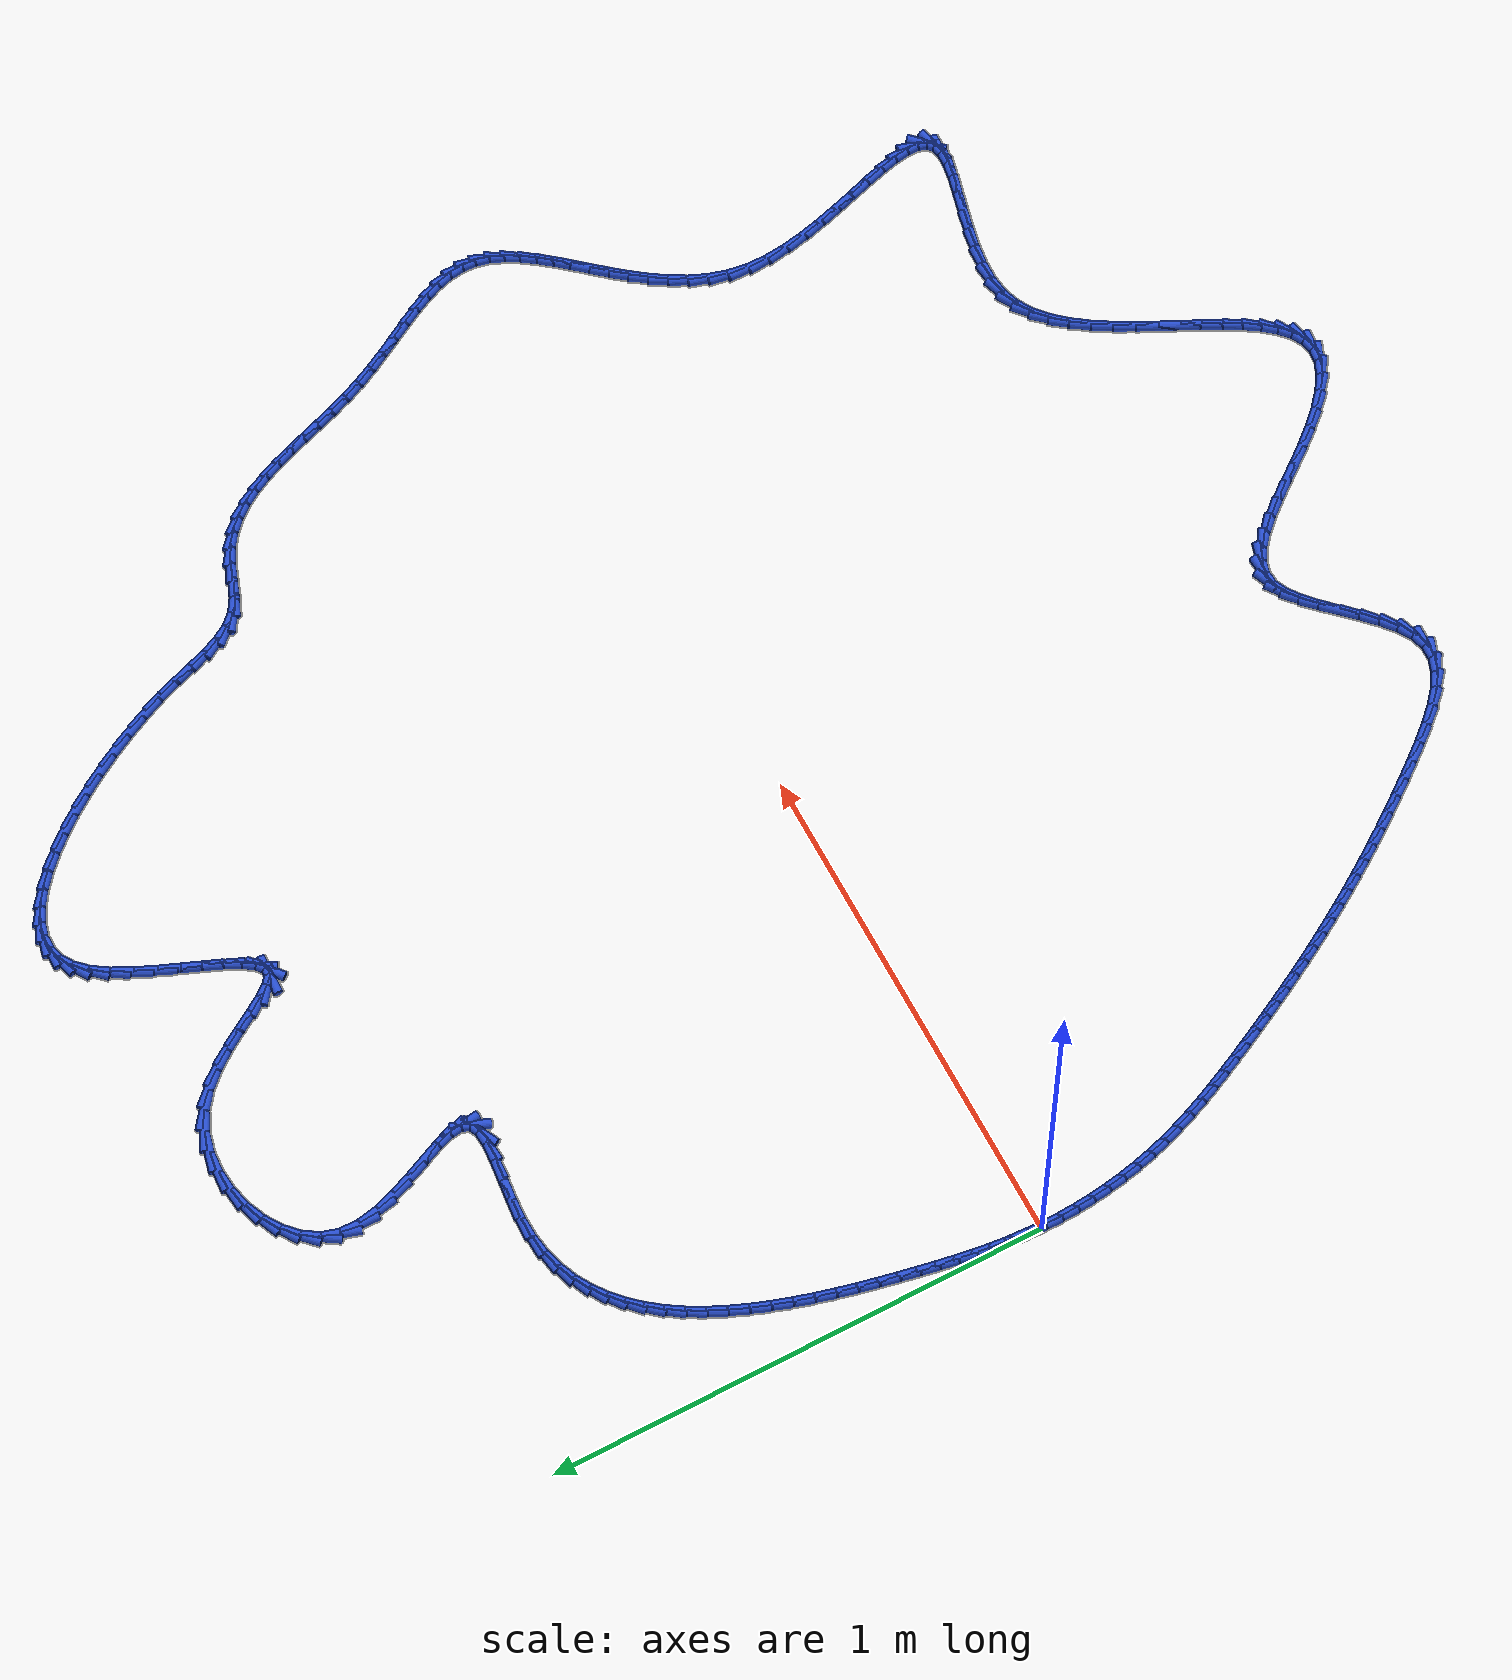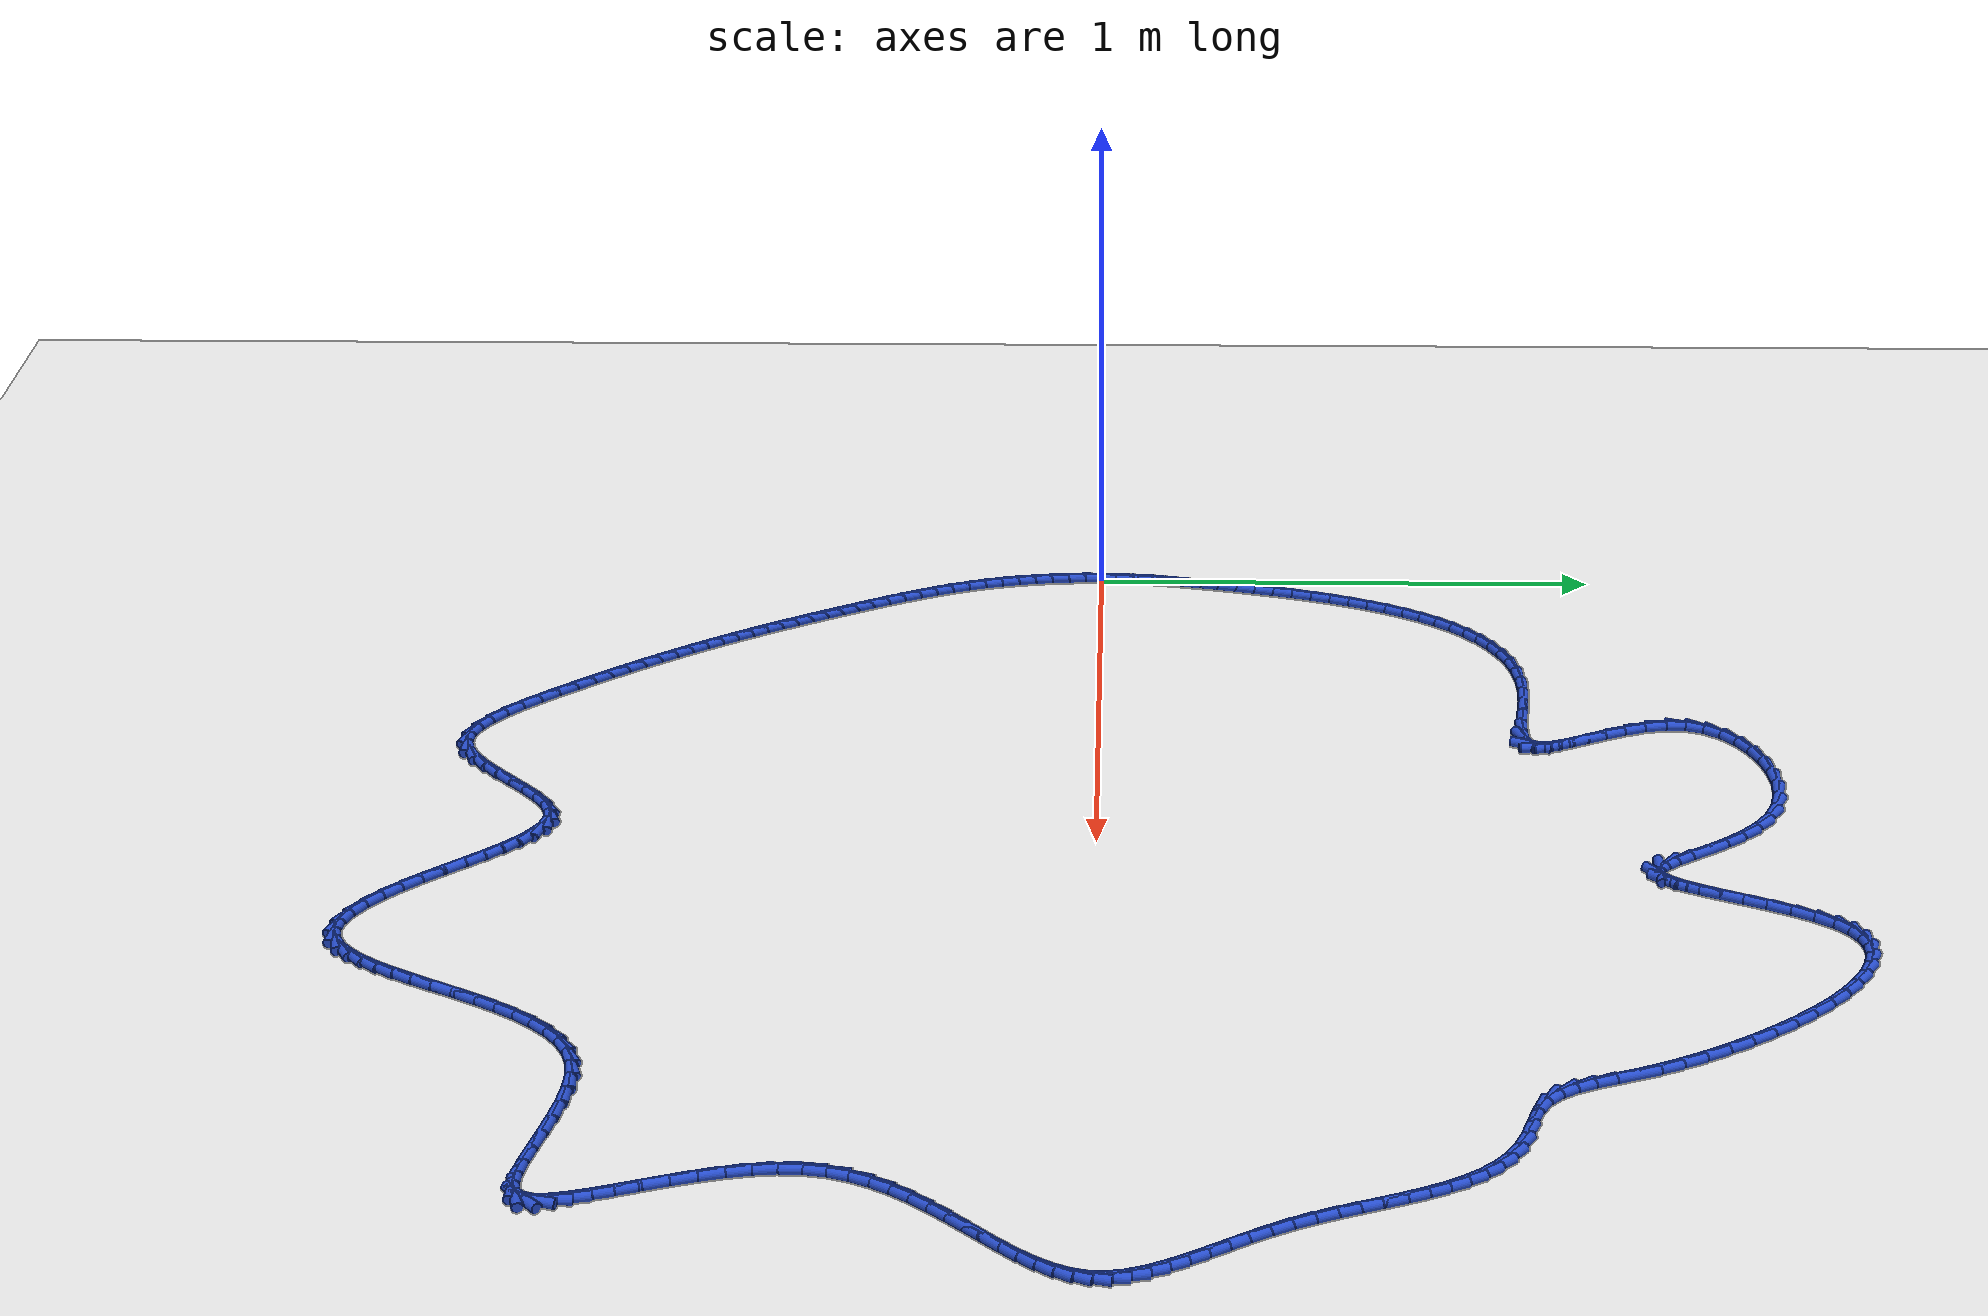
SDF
<sdf version="1.6">
 <world name="default">
  <light name="sun" type="directional">
   <pose>0 0 10 0 -0 0</pose>
   <diffuse>0.8 0.8 0.8 1</diffuse>
   <specular>0.2 0.2 0.2 1</specular>
   <attenuation>
    <range>1000</range>
    <constant>0.9</constant>
    <linear>0.01</linear>
    <quadratic>0.001</quadratic>
   </attenuation>
   <direction>-0.5 0.1 -0.9</direction>
  </light>
  <model name="ground_plane">
   <static>1</static>
   <link name="link">
    <collision name="collision">
     <geometry><plane><normal>0 0 1</normal><size>100 100</size></plane></geometry>
     <surface><friction><ode><mu>100</mu><mu2>50</mu2></ode></friction></surface>
    </collision>
    <visual name="visual">
     <cast_shadows>0</cast_shadows>
     <geometry><plane><normal>0 0 1</normal><size>100 100</size></plane></geometry>
     <material>
      <script><uri>file://media/materials/scripts/gazebo.material</uri><name>Gazebo/WhiteGlow</name></script>
     </material>
    </visual>
   </link>
  </model>
  <gravity>0 0 -9.8</gravity>
  <magnetic_field>6e-06 2.3e-05 -4.2e-05</magnetic_field>
  <atmosphere type="adiabatic"/>
  <physics name="default_physics" default="0" type="ode">
   <max_step_size>0.001</max_step_size>
   <real_time_factor>1</real_time_factor>
   <real_time_update_rate>1000</real_time_update_rate>
  </physics>
  <scene><ambient>0.4 0.4 0.4 1</ambient><background>0.7 0.7 0.7 1</background><shadows>1</shadows></scene>
  <spherical_coordinates>
   <surface_model>EARTH_WGS84</surface_model>
   <latitude_deg>0</latitude_deg>
   <longitude_deg>0</longitude_deg>
   <elevation>0</elevation>
   <heading_deg>0</heading_deg>
  </spherical_coordinates>
  <model name="line">
   <link name="link_0">
    <pose>0.0 -4.85722573273506e-17 0.01 0 1.57 1.5344831415001807</pose>
    <collision name="collision">
     <geometry><cylinder><radius>0.01</radius><length>0.08</length></cylinder></geometry>
    </collision>
    <visual name="visual">
     <material>
      <script><name>Gazebo/Blue</name><uri>file://media/materials/scripts/gazebo.material</uri></script>
     </material>
     <geometry><cylinder><radius>0.01</radius><length>0.08</length></cylinder></geometry>
    </visual>
   </link>
   <link name="link_1">
    <pose>0.001230028604127636 0.03385789179870531 0.01 0 1.57 1.4982256026668357</pose>
    <collision name="collision">
     <geometry><cylinder><radius>0.01</radius><length>0.08</length></cylinder></geometry>
    </collision>
    <visual name="visual">
     <material>
      <script><name>Gazebo/Blue</name><uri>file://media/materials/scripts/gazebo.material</uri></script>
     </material>
     <geometry><cylinder><radius>0.01</radius><length>0.08</length></cylinder></geometry>
    </visual>
   </link>
   <link name="link_2">
    <pose>0.0036779097574545115 0.06752962939858016 0.01 0 1.57 1.4656631178485222</pose>
    <collision name="collision">
     <geometry><cylinder><radius>0.01</radius><length>0.08</length></cylinder></geometry>
    </collision>
    <visual name="visual">
     <material>
      <script><name>Gazebo/Blue</name><uri>file://media/materials/scripts/gazebo.material</uri></script>
     </material>
     <geometry><cylinder><radius>0.01</radius><length>0.08</length></cylinder></geometry>
    </visual>
   </link>
   <link name="link_3">
    <pose>0.007231691294133859 0.10120765186294339 0.01 0 1.57 1.4373507270346766</pose>
    <collision name="collision">
     <geometry><cylinder><radius>0.01</radius><length>0.08</length></cylinder></geometry>
    </collision>
    <visual name="visual">
     <material>
      <script><name>Gazebo/Blue</name><uri>file://media/materials/scripts/gazebo.material</uri></script>
     </material>
     <geometry><cylinder><radius>0.01</radius><length>0.08</length></cylinder></geometry>
    </visual>
   </link>
   <link name="link_4">
    <pose>0.01177942104831893 0.13508439825511404 0.01 0 1.57 1.4136534350680687</pose>
    <collision name="collision">
     <geometry><cylinder><radius>0.01</radius><length>0.08</length></cylinder></geometry>
    </collision>
    <visual name="visual">
     <material>
      <script><name>Gazebo/Blue</name><uri>file://media/materials/scripts/gazebo.material</uri></script>
     </material>
     <geometry><cylinder><radius>0.01</radius><length>0.08</length></cylinder></geometry>
    </visual>
   </link>
   <link name="link_5">
    <pose>0.01720914685416297 0.16935230763841097 0.01 0 1.57 1.3947469647410982</pose>
    <collision name="collision">
     <geometry><cylinder><radius>0.01</radius><length>0.08</length></cylinder></geometry>
    </collision>
    <visual name="visual">
     <material>
      <script><name>Gazebo/Blue</name><uri>file://media/materials/scripts/gazebo.material</uri></script>
     </material>
     <geometry><cylinder><radius>0.01</radius><length>0.08</length></cylinder></geometry>
    </visual>
   </link>
   <link name="link_6">
    <pose>0.023408916545819225 0.20420381907615312 0.01 0 1.57 1.3806345713154973</pose>
    <collision name="collision">
     <geometry><cylinder><radius>0.01</radius><length>0.08</length></cylinder></geometry>
    </collision>
    <visual name="visual">
     <material>
      <script><name>Gazebo/Blue</name><uri>file://media/materials/scripts/gazebo.material</uri></script>
     </material>
     <geometry><cylinder><radius>0.01</radius><length>0.08</length></cylinder></geometry>
    </visual>
   </link>
   <link name="link_7">
    <pose>0.030266777957440927 0.2398313716316595 0.01 0 1.57 1.3710185096209477</pose>
    <collision name="collision">
     <geometry><cylinder><radius>0.01</radius><length>0.08</length></cylinder></geometry>
    </collision>
    <visual name="visual">
     <material>
      <script><name>Gazebo/Blue</name><uri>file://media/materials/scripts/gazebo.material</uri></script>
     </material>
     <geometry><cylinder><radius>0.01</radius><length>0.08</length></cylinder></geometry>
    </visual>
   </link>
   <link name="link_8">
    <pose>0.03767494799383224 0.2764187698021842 0.01 0 1.57 1.3617506165100015</pose>
    <collision name="collision">
     <geometry><cylinder><radius>0.01</radius><length>0.08</length></cylinder></geometry>
    </collision>
    <visual name="visual">
     <material>
      <script><name>Gazebo/Blue</name><uri>file://media/materials/scripts/gazebo.material</uri></script>
     </material>
     <geometry><cylinder><radius>0.01</radius><length>0.08</length></cylinder></geometry>
    </visual>
   </link>
   <link name="link_9">
    <pose>0.04563246628902441 0.3139285774320988 0.01 0 1.57 1.3486553953474039</pose>
    <collision name="collision">
     <geometry><cylinder><radius>0.01</radius><length>0.08</length></cylinder></geometry>
    </collision>
    <visual name="visual">
     <material>
      <script><name>Gazebo/Blue</name><uri>file://media/materials/scripts/gazebo.material</uri></script>
     </material>
     <geometry><cylinder><radius>0.01</radius><length>0.08</length></cylinder></geometry>
    </visual>
   </link>
   <link name="link_10">
    <pose>0.05425164777208343 0.35208875379790483 0.01 0 1.57 1.3315220033120312</pose>
    <collision name="collision">
     <geometry><cylinder><radius>0.01</radius><length>0.08</length></cylinder></geometry>
    </collision>
    <visual name="visual">
     <material>
      <script><name>Gazebo/Blue</name><uri>file://media/materials/scripts/gazebo.material</uri></script>
     </material>
     <geometry><cylinder><radius>0.01</radius><length>0.08</length></cylinder></geometry>
    </visual>
   </link>
   <link name="link_11">
    <pose>0.06365026834764892 0.3906159479445643 0.01 0 1.57 1.3102034624673788</pose>
    <collision name="collision">
     <geometry><cylinder><radius>0.01</radius><length>0.08</length></cylinder></geometry>
    </collision>
    <visual name="visual">
     <material>
      <script><name>Gazebo/Blue</name><uri>file://media/materials/scripts/gazebo.material</uri></script>
     </material>
     <geometry><cylinder><radius>0.01</radius><length>0.08</length></cylinder></geometry>
    </visual>
   </link>
   <link name="link_12">
    <pose>0.07394610392036047 0.4292268089170389 0.01 0 1.57 1.284423318271676</pose>
    <collision name="collision">
     <geometry><cylinder><radius>0.01</radius><length>0.08</length></cylinder></geometry>
    </collision>
    <visual name="visual">
     <material>
      <script><name>Gazebo/Blue</name><uri>file://media/materials/scripts/gazebo.material</uri></script>
     </material>
     <geometry><cylinder><radius>0.01</radius><length>0.08</length></cylinder></geometry>
    </visual>
   </link>
   <link name="link_13">
    <pose>0.08525693039485763 0.46763798576029014 0.01 0 1.57 1.2537781405655828</pose>
    <collision name="collision">
     <geometry><cylinder><radius>0.01</radius><length>0.08</length></cylinder></geometry>
    </collision>
    <visual name="visual">
     <material>
      <script><name>Gazebo/Blue</name><uri>file://media/materials/scripts/gazebo.material</uri></script>
     </material>
     <geometry><cylinder><radius>0.01</radius><length>0.08</length></cylinder></geometry>
    </visual>
   </link>
   <link name="link_14">
    <pose>0.09770052367578003 0.5055661275192804 0.01 0 1.57 1.2177357412604168</pose>
    <collision name="collision">
     <geometry><cylinder><radius>0.01</radius><length>0.08</length></cylinder></geometry>
    </collision>
    <visual name="visual">
     <material>
      <script><name>Gazebo/Blue</name><uri>file://media/materials/scripts/gazebo.material</uri></script>
     </material>
     <geometry><cylinder><radius>0.01</radius><length>0.08</length></cylinder></geometry>
    </visual>
   </link>
   <link name="link_15">
    <pose>0.11139465966776724 0.5427278832389709 0.01 0 1.57 1.175632929030025</pose>
    <collision name="collision">
     <geometry><cylinder><radius>0.01</radius><length>0.08</length></cylinder></geometry>
    </collision>
    <visual name="visual">
     <material>
      <script><name>Gazebo/Blue</name><uri>file://media/materials/scripts/gazebo.material</uri></script>
     </material>
     <geometry><cylinder><radius>0.01</radius><length>0.08</length></cylinder></geometry>
    </visual>
   </link>
   <link name="link_16">
    <pose>0.1264571142754589 0.5788399019643242 0.01 0 1.57 1.1266782590041369</pose>
    <collision name="collision">
     <geometry><cylinder><radius>0.01</radius><length>0.08</length></cylinder></geometry>
    </collision>
    <visual name="visual">
     <material>
      <script><name>Gazebo/Blue</name><uri>file://media/materials/scripts/gazebo.material</uri></script>
     </material>
     <geometry><cylinder><radius>0.01</radius><length>0.08</length></cylinder></geometry>
    </visual>
   </link>
   <link name="link_17">
    <pose>0.14300566340349452 0.6136188327403014 0.01 0 1.57 1.0699683712431356</pose>
    <collision name="collision">
     <geometry><cylinder><radius>0.01</radius><length>0.08</length></cylinder></geometry>
    </collision>
    <visual name="visual">
     <material>
      <script><name>Gazebo/Blue</name><uri>file://media/materials/scripts/gazebo.material</uri></script>
     </material>
     <geometry><cylinder><radius>0.01</radius><length>0.08</length></cylinder></geometry>
    </visual>
   </link>
   <link name="link_18">
    <pose>0.16115808295651374 0.6467813246118644 0.01 0 1.57 1.0045312615722355</pose>
    <collision name="collision">
     <geometry><cylinder><radius>0.01</radius><length>0.08</length></cylinder></geometry>
    </collision>
    <visual name="visual">
     <material>
      <script><name>Gazebo/Blue</name><uri>file://media/materials/scripts/gazebo.material</uri></script>
     </material>
     <geometry><cylinder><radius>0.01</radius><length>0.08</length></cylinder></geometry>
    </visual>
   </link>
   <link name="link_19">
    <pose>0.1810321488391562 0.6780440266239756 0.01 0 1.57 0.929415427886102</pose>
    <collision name="collision">
     <geometry><cylinder><radius>0.01</radius><length>0.08</length></cylinder></geometry>
    </collision>
    <visual name="visual">
     <material>
      <script><name>Gazebo/Blue</name><uri>file://media/materials/scripts/gazebo.material</uri></script>
     </material>
     <geometry><cylinder><radius>0.01</radius><length>0.08</length></cylinder></geometry>
    </visual>
   </link>
   <link name="link_20">
    <pose>0.20274563695606135 0.707123587821596 0.01 0 1.57 0.843847093934799</pose>
    <collision name="collision">
     <geometry><cylinder><radius>0.01</radius><length>0.08</length></cylinder></geometry>
    </collision>
    <visual name="visual">
     <material>
      <script><name>Gazebo/Blue</name><uri>file://media/materials/scripts/gazebo.material</uri></script>
     </material>
     <geometry><cylinder><radius>0.01</radius><length>0.08</length></cylinder></geometry>
    </visual>
   </link>
   <link name="link_21">
    <pose>0.2264163232118689 0.7337366572496882 0.01 0 1.57 0.7474708683350556</pose>
    <collision name="collision">
     <geometry><cylinder><radius>0.01</radius><length>0.08</length></cylinder></geometry>
    </collision>
    <visual name="visual">
     <material>
      <script><name>Gazebo/Blue</name><uri>file://media/materials/scripts/gazebo.material</uri></script>
     </material>
     <geometry><cylinder><radius>0.01</radius><length>0.08</length></cylinder></geometry>
    </visual>
   </link>
   <link name="link_22">
    <pose>0.25216198351121843 0.7575998839532133 0.01 0 1.57 0.6406597021847755</pose>
    <collision name="collision">
     <geometry><cylinder><radius>0.01</radius><length>0.08</length></cylinder></geometry>
    </collision>
    <visual name="visual">
     <material>
      <script><name>Gazebo/Blue</name><uri>file://media/materials/scripts/gazebo.material</uri></script>
     </material>
     <geometry><cylinder><radius>0.01</radius><length>0.08</length></cylinder></geometry>
    </visual>
   </link>
   <link name="link_23">
    <pose>0.28010039375874946 0.7784299169771336 0.01 0 1.57 0.5248192050671189</pose>
    <collision name="collision">
     <geometry><cylinder><radius>0.01</radius><length>0.08</length></cylinder></geometry>
    </collision>
    <visual name="visual">
     <material>
      <script><name>Gazebo/Blue</name><uri>file://media/materials/scripts/gazebo.material</uri></script>
     </material>
     <geometry><cylinder><radius>0.01</radius><length>0.08</length></cylinder></geometry>
    </visual>
   </link>
   <link name="link_24">
    <pose>0.3103493298591018 0.7959434053664107 0.01 0 1.57 0.4025383427622606</pose>
    <collision name="collision">
     <geometry><cylinder><radius>0.01</radius><length>0.08</length></cylinder></geometry>
    </collision>
    <visual name="visual">
     <material>
      <script><name>Gazebo/Blue</name><uri>file://media/materials/scripts/gazebo.material</uri></script>
     </material>
     <geometry><cylinder><radius>0.01</radius><length>0.08</length></cylinder></geometry>
    </visual>
   </link>
   <link name="link_25">
    <pose>0.34302656771691487 0.8098569981660068 0.01 0 1.57 0.27742124114967753</pose>
    <collision name="collision">
     <geometry><cylinder><radius>0.01</radius><length>0.08</length></cylinder></geometry>
    </collision>
    <visual name="visual">
     <material>
      <script><name>Gazebo/Blue</name><uri>file://media/materials/scripts/gazebo.material</uri></script>
     </material>
     <geometry><cylinder><radius>0.01</radius><length>0.08</length></cylinder></geometry>
    </visual>
   </link>
   <link name="link_26">
    <pose>0.37824988323682796 0.8198873444208827 0.01 0 1.57 0.15355044070518425</pose>
    <collision name="collision">
     <geometry><cylinder><radius>0.01</radius><length>0.08</length></cylinder></geometry>
    </collision>
    <visual name="visual">
     <material>
      <script><name>Gazebo/Blue</name><uri>file://media/materials/scripts/gazebo.material</uri></script>
     </material>
     <geometry><cylinder><radius>0.01</radius><length>0.08</length></cylinder></geometry>
    </visual>
   </link>
   <link name="link_27">
    <pose>0.41613705232348136 0.8257510931760015 0.01 0 1.57 0.03486780161515597</pose>
    <collision name="collision">
     <geometry><cylinder><radius>0.01</radius><length>0.08</length></cylinder></geometry>
    </collision>
    <visual name="visual">
     <material>
      <script><name>Gazebo/Blue</name><uri>file://media/materials/scripts/gazebo.material</uri></script>
     </material>
     <geometry><cylinder><radius>0.01</radius><length>0.08</length></cylinder></geometry>
    </visual>
   </link>
   <link name="link_28">
    <pose>0.456800994854266 0.8271695303317333 0.01 0 1.57 -0.06015945254124833</pose>
    <collision name="collision">
     <geometry><cylinder><radius>0.01</radius><length>0.08</length></cylinder></geometry>
    </collision>
    <visual name="visual">
     <material>
      <script><name>Gazebo/Blue</name><uri>file://media/materials/scripts/gazebo.material</uri></script>
     </material>
     <geometry><cylinder><radius>0.01</radius><length>0.08</length></cylinder></geometry>
    </visual>
   </link>
   <link name="link_29">
    <pose>0.49959201691257177 0.8245921357863724 0.01 0 1.57 -0.10757312567995905</pose>
    <collision name="collision">
     <geometry><cylinder><radius>0.01</radius><length>0.08</length></cylinder></geometry>
    </collision>
    <visual name="visual">
     <material>
      <script><name>Gazebo/Blue</name><uri>file://media/materials/scripts/gazebo.material</uri></script>
     </material>
     <geometry><cylinder><radius>0.01</radius><length>0.08</length></cylinder></geometry>
    </visual>
   </link>
   <link name="link_30">
    <pose>0.5422743588851907 0.8199828696766477 0.01 0 1.57 -0.11135375276267728</pose>
    <collision name="collision">
     <geometry><cylinder><radius>0.01</radius><length>0.08</length></cylinder></geometry>
    </collision>
    <visual name="visual">
     <material>
      <script><name>Gazebo/Blue</name><uri>file://media/materials/scripts/gazebo.material</uri></script>
     </material>
     <geometry><cylinder><radius>0.01</radius><length>0.08</length></cylinder></geometry>
    </visual>
   </link>
   <link name="link_31">
    <pose>0.582414476034081 0.8154945504341625 0.01 0 1.57 -0.06289418981075924</pose>
    <collision name="collision">
     <geometry><cylinder><radius>0.01</radius><length>0.08</length></cylinder></geometry>
    </collision>
    <visual name="visual">
     <material>
      <script><name>Gazebo/Blue</name><uri>file://media/materials/scripts/gazebo.material</uri></script>
     </material>
     <geometry><cylinder><radius>0.01</radius><length>0.08</length></cylinder></geometry>
    </visual>
   </link>
   <link name="link_32">
    <pose>0.6175788236212011 0.8132799964905195 0.01 0 1.57 0.07953022639570836</pose>
    <collision name="collision">
     <geometry><cylinder><radius>0.01</radius><length>0.08</length></cylinder></geometry>
    </collision>
    <visual name="visual">
     <material>
      <script><name>Gazebo/Blue</name><uri>file://media/materials/scripts/gazebo.material</uri></script>
     </material>
     <geometry><cylinder><radius>0.01</radius><length>0.08</length></cylinder></geometry>
    </visual>
   </link>
   <link name="link_33">
    <pose>0.6453338569085092 0.815492026277322 0.01 0 1.57 0.4562666971590935</pose>
    <collision name="collision">
     <geometry><cylinder><radius>0.01</radius><length>0.08</length></cylinder></geometry>
    </collision>
    <visual name="visual">
     <material>
      <script><name>Gazebo/Blue</name><uri>file://media/materials/scripts/gazebo.material</uri></script>
     </material>
     <geometry><cylinder><radius>0.01</radius><length>0.08</length></cylinder></geometry>
    </visual>
   </link>
   <link name="link_34">
    <pose>0.6632460314798072 0.8242834580002737 0.01 0 1.57 1.2048317003839442</pose>
    <collision name="collision">
     <geometry><cylinder><radius>0.01</radius><length>0.08</length></cylinder></geometry>
    </collision>
    <visual name="visual">
     <material>
      <script><name>Gazebo/Blue</name><uri>file://media/materials/scripts/gazebo.material</uri></script>
     </material>
     <geometry><cylinder><radius>0.01</radius><length>0.08</length></cylinder></geometry>
    </visual>
   </link>
   <link name="link_35">
    <pose>0.6697327051443129 0.8412098688993299 0.01 0 1.57 -1.440100866369434</pose>
    <collision name="collision">
     <geometry><cylinder><radius>0.01</radius><length>0.08</length></cylinder></geometry>
    </collision>
    <visual name="visual">
     <material>
      <script><name>Gazebo/Blue</name><uri>file://media/materials/scripts/gazebo.material</uri></script>
     </material>
     <geometry><cylinder><radius>0.01</radius><length>0.08</length></cylinder></geometry>
    </visual>
   </link>
   <link name="link_36">
    <pose>0.6665412741723855 0.8654895108119429 0.01 0 1.57 -1.2426842140372603</pose>
    <collision name="collision">
     <geometry><cylinder><radius>0.01</radius><length>0.08</length></cylinder></geometry>
    </collision>
    <visual name="visual">
     <material>
      <script><name>Gazebo/Blue</name><uri>file://media/materials/scripts/gazebo.material</uri></script>
     </material>
     <geometry><cylinder><radius>0.01</radius><length>0.08</length></cylinder></geometry>
    </visual>
   </link>
   <link name="link_37">
    <pose>0.6562336477006269 0.8957689359885624 0.01 0 1.57 -1.1684779681116715</pose>
    <collision name="collision">
     <geometry><cylinder><radius>0.01</radius><length>0.08</length></cylinder></geometry>
    </collision>
    <visual name="visual">
     <material>
      <script><name>Gazebo/Blue</name><uri>file://media/materials/scripts/gazebo.material</uri></script>
     </material>
     <geometry><cylinder><radius>0.01</radius><length>0.08</length></cylinder></geometry>
    </visual>
   </link>
   <link name="link_38">
    <pose>0.6413717348656395 0.9306946966796384 0.01 0 1.57 -1.1554548927862949</pose>
    <collision name="collision">
     <geometry><cylinder><radius>0.01</radius><length>0.08</length></cylinder></geometry>
    </collision>
    <visual name="visual">
     <material>
      <script><name>Gazebo/Blue</name><uri>file://media/materials/scripts/gazebo.material</uri></script>
     </material>
     <geometry><cylinder><radius>0.01</radius><length>0.08</length></cylinder></geometry>
    </visual>
   </link>
   <link name="link_39">
    <pose>0.6245174448040254 0.9689133451356217 0.01 0 1.57 -1.1855436105739772</pose>
    <collision name="collision">
     <geometry><cylinder><radius>0.01</radius><length>0.08</length></cylinder></geometry>
    </collision>
    <visual name="visual">
     <material>
      <script><name>Gazebo/Blue</name><uri>file://media/materials/scripts/gazebo.material</uri></script>
     </material>
     <geometry><cylinder><radius>0.01</radius><length>0.08</length></cylinder></geometry>
    </visual>
   </link>
   <link name="link_40">
    <pose>0.6082326866523867 1.009071433606961 0.01 0 1.57 -1.258530468710658</pose>
    <collision name="collision">
     <geometry><cylinder><radius>0.01</radius><length>0.08</length></cylinder></geometry>
    </collision>
    <visual name="visual">
     <material>
      <script><name>Gazebo/Blue</name><uri>file://media/materials/scripts/gazebo.material</uri></script>
     </material>
     <geometry><cylinder><radius>0.01</radius><length>0.08</length></cylinder></geometry>
    </visual>
   </link>
   <link name="link_41">
    <pose>0.5950793695473258 1.0498155143441084 0.01 0 1.57 -1.3863100078885935</pose>
    <collision name="collision">
     <geometry><cylinder><radius>0.01</radius><length>0.08</length></cylinder></geometry>
    </collision>
    <visual name="visual">
     <material>
      <script><name>Gazebo/Blue</name><uri>file://media/materials/scripts/gazebo.material</uri></script>
     </material>
     <geometry><cylinder><radius>0.01</radius><length>0.08</length></cylinder></geometry>
    </visual>
   </link>
   <link name="link_42">
    <pose>0.5876194026254445 1.089792139597512 0.01 0 1.57 1.5498086764448906</pose>
    <collision name="collision">
     <geometry><cylinder><radius>0.01</radius><length>0.08</length></cylinder></geometry>
    </collision>
    <visual name="visual">
     <material>
      <script><name>Gazebo/Blue</name><uri>file://media/materials/scripts/gazebo.material</uri></script>
     </material>
     <geometry><cylinder><radius>0.01</radius><length>0.08</length></cylinder></geometry>
    </visual>
   </link>
   <link name="link_43">
    <pose>0.5884140249417595 1.1276480037606915 0.01 0 1.57 1.2702454409805772</pose>
    <collision name="collision">
     <geometry><cylinder><radius>0.01</radius><length>0.08</length></cylinder></geometry>
    </collision>
    <visual name="visual">
     <material>
      <script><name>Gazebo/Blue</name><uri>file://media/materials/scripts/gazebo.material</uri></script>
     </material>
     <geometry><cylinder><radius>0.01</radius><length>0.08</length></cylinder></geometry>
    </visual>
   </link>
   <link name="link_44">
    <pose>0.5991291805111367 1.1622197183760172 0.01 0 1.57 1.0015167624361119</pose>
    <collision name="collision">
     <geometry><cylinder><radius>0.01</radius><length>0.08</length></cylinder></geometry>
    </collision>
    <visual name="visual">
     <material>
      <script><name>Gazebo/Blue</name><uri>file://media/materials/scripts/gazebo.material</uri></script>
     </material>
     <geometry><cylinder><radius>0.01</radius><length>0.08</length></cylinder></geometry>
    </visual>
   </link>
   <link name="link_45">
    <pose>0.6187686229902907 1.1929086201098107 0.01 0 1.57 0.7711072919826788</pose>
    <collision name="collision">
     <geometry><cylinder><radius>0.01</radius><length>0.08</length></cylinder></geometry>
    </collision>
    <visual name="visual">
     <material>
      <script><name>Gazebo/Blue</name><uri>file://media/materials/scripts/gazebo.material</uri></script>
     </material>
     <geometry><cylinder><radius>0.01</radius><length>0.08</length></cylinder></geometry>
    </visual>
   </link>
   <link name="link_46">
    <pose>0.6458435331864244 1.2192205341232316 0.01 0 1.57 0.5758798483706761</pose>
    <collision name="collision">
     <geometry><cylinder><radius>0.01</radius><length>0.08</length></cylinder></geometry>
    </collision>
    <visual name="visual">
     <material>
      <script><name>Gazebo/Blue</name><uri>file://media/materials/scripts/gazebo.material</uri></script>
     </material>
     <geometry><cylinder><radius>0.01</radius><length>0.08</length></cylinder></geometry>
    </visual>
   </link>
   <link name="link_47">
    <pose>0.6788650919067416 1.24066128557744 0.01 0 1.57 0.4051807091700433</pose>
    <collision name="collision">
     <geometry><cylinder><radius>0.01</radius><length>0.08</length></cylinder></geometry>
    </collision>
    <visual name="visual">
     <material>
      <script><name>Gazebo/Blue</name><uri>file://media/materials/scripts/gazebo.material</uri></script>
     </material>
     <geometry><cylinder><radius>0.01</radius><length>0.08</length></cylinder></geometry>
    </visual>
   </link>
   <link name="link_48">
    <pose>0.7163444799584449 1.2567366996335945 0.01 0 1.57 0.2473925315085086</pose>
    <collision name="collision">
     <geometry><cylinder><radius>0.01</radius><length>0.08</length></cylinder></geometry>
    </collision>
    <visual name="visual">
     <material>
      <script><name>Gazebo/Blue</name><uri>file://media/materials/scripts/gazebo.material</uri></script>
     </material>
     <geometry><cylinder><radius>0.01</radius><length>0.08</length></cylinder></geometry>
    </visual>
   </link>
   <link name="link_49">
    <pose>0.7567928781487374 1.2669526014528556 0.01 0 1.57 0.09185490037564378</pose>
    <collision name="collision">
     <geometry><cylinder><radius>0.01</radius><length>0.08</length></cylinder></geometry>
    </collision>
    <visual name="visual">
     <material>
      <script><name>Gazebo/Blue</name><uri>file://media/materials/scripts/gazebo.material</uri></script>
     </material>
     <geometry><cylinder><radius>0.01</radius><length>0.08</length></cylinder></geometry>
    </visual>
   </link>
   <link name="link_50">
    <pose>0.7987214672848227 1.2708148161963824 0.01 0 1.57 -0.07110250183224795</pose>
    <collision name="collision">
     <geometry><cylinder><radius>0.01</radius><length>0.08</length></cylinder></geometry>
    </collision>
    <visual name="visual">
     <material>
      <script><name>Gazebo/Blue</name><uri>file://media/materials/scripts/gazebo.material</uri></script>
     </material>
     <geometry><cylinder><radius>0.01</radius><length>0.08</length></cylinder></geometry>
    </visual>
   </link>
   <link name="link_51">
    <pose>0.8406414281739035 1.2678291690253343 0.01 0 1.57 -0.250142167579732</pose>
    <collision name="collision">
     <geometry><cylinder><radius>0.01</radius><length>0.08</length></cylinder></geometry>
    </collision>
    <visual name="visual">
     <material>
      <script><name>Gazebo/Blue</name><uri>file://media/materials/scripts/gazebo.material</uri></script>
     </material>
     <geometry><cylinder><radius>0.01</radius><length>0.08</length></cylinder></geometry>
    </visual>
   </link>
   <link name="link_52">
    <pose>0.8810639416231834 1.257501485100871 0.01 0 1.57 -0.4517330003039419</pose>
    <collision name="collision">
     <geometry><cylinder><radius>0.01</radius><length>0.08</length></cylinder></geometry>
    </collision>
    <visual name="visual">
     <material>
      <script><name>Gazebo/Blue</name><uri>file://media/materials/scripts/gazebo.material</uri></script>
     </material>
     <geometry><cylinder><radius>0.01</radius><length>0.08</length></cylinder></geometry>
    </visual>
   </link>
   <link name="link_53">
    <pose>0.9185002101703883 1.239337623199597 0.01 0 1.57 -0.6610865135040858</pose>
    <collision name="collision">
     <geometry><cylinder><radius>0.01</radius><length>0.08</length></cylinder></geometry>
    </collision>
    <visual name="visual">
     <material>
      <script><name>Gazebo/Blue</name><uri>file://media/materials/scripts/gazebo.material</uri></script>
     </material>
     <geometry><cylinder><radius>0.01</radius><length>0.08</length></cylinder></geometry>
    </visual>
   </link>
   <link name="link_54">
    <pose>0.951829377572703 1.2134126188041072 0.01 0 1.57 -0.8212805109000028</pose>
    <collision name="collision">
     <geometry><cylinder><radius>0.01</radius><length>0.08</length></cylinder></geometry>
    </collision>
    <visual name="visual">
     <material>
      <script><name>Gazebo/Blue</name><uri>file://media/materials/scripts/gazebo.material</uri></script>
     </material>
     <geometry><cylinder><radius>0.01</radius><length>0.08</length></cylinder></geometry>
    </visual>
   </link>
   <link name="link_55">
    <pose>0.9812341847487689 1.1818180717259201 0.01 0 1.57 -0.929008160906967</pose>
    <collision name="collision">
     <geometry><cylinder><radius>0.01</radius><length>0.08</length></cylinder></geometry>
    </collision>
    <visual name="visual">
     <material>
      <script><name>Gazebo/Blue</name><uri>file://media/materials/scripts/gazebo.material</uri></script>
     </material>
     <geometry><cylinder><radius>0.01</radius><length>0.08</length></cylinder></geometry>
    </visual>
   </link>
   <link name="link_56">
    <pose>1.0071859373438081 1.147091969166315 0.01 0 1.57 -0.99417797046157</pose>
    <collision name="collision">
     <geometry><cylinder><radius>0.01</radius><length>0.08</length></cylinder></geometry>
    </collision>
    <visual name="visual">
     <material>
      <script><name>Gazebo/Blue</name><uri>file://media/materials/scripts/gazebo.material</uri></script>
     </material>
     <geometry><cylinder><radius>0.01</radius><length>0.08</length></cylinder></geometry>
    </visual>
   </link>
   <link name="link_57">
    <pose>1.0301559410030408 1.111772298326571 0.01 0 1.57 -1.0208612360913005</pose>
    <collision name="collision">
     <geometry><cylinder><radius>0.01</radius><length>0.08</length></cylinder></geometry>
    </collision>
    <visual name="visual">
     <material>
      <script><name>Gazebo/Blue</name><uri>file://media/materials/scripts/gazebo.material</uri></script>
     </material>
     <geometry><cylinder><radius>0.01</radius><length>0.08</length></cylinder></geometry>
    </visual>
   </link>
   <link name="link_58">
    <pose>1.0506155013716885 1.0783970464079673 0.01 0 1.57 -1.0032283463574</pose>
    <collision name="collision">
     <geometry><cylinder><radius>0.01</radius><length>0.08</length></cylinder></geometry>
    </collision>
    <visual name="visual">
     <material>
      <script><name>Gazebo/Blue</name><uri>file://media/materials/scripts/gazebo.material</uri></script>
     </material>
     <geometry><cylinder><radius>0.01</radius><length>0.08</length></cylinder></geometry>
    </visual>
   </link>
   <link name="link_59">
    <pose>1.0690359240949716 1.0495042006117834 0.01 0 1.57 -0.9143076333291085</pose>
    <collision name="collision">
     <geometry><cylinder><radius>0.01</radius><length>0.08</length></cylinder></geometry>
    </collision>
    <visual name="visual">
     <material>
      <script><name>Gazebo/Blue</name><uri>file://media/materials/scripts/gazebo.material</uri></script>
     </material>
     <geometry><cylinder><radius>0.01</radius><length>0.08</length></cylinder></geometry>
    </visual>
   </link>
   <link name="link_60">
    <pose>1.0858885148181117 1.0276317481392983 0.01 0 1.57 -0.6633861019622189</pose>
    <collision name="collision">
     <geometry><cylinder><radius>0.01</radius><length>0.08</length></cylinder></geometry>
    </collision>
    <visual name="visual">
     <material>
      <script><name>Gazebo/Blue</name><uri>file://media/materials/scripts/gazebo.material</uri></script>
     </material>
     <geometry><cylinder><radius>0.01</radius><length>0.08</length></cylinder></geometry>
    </visual>
   </link>
   <link name="link_61">
    <pose>1.1016445791863296 1.0153176761917921 0.01 0 1.57 -0.019727249602444423</pose>
    <collision name="collision">
     <geometry><cylinder><radius>0.01</radius><length>0.08</length></cylinder></geometry>
    </collision>
    <visual name="visual">
     <material>
      <script><name>Gazebo/Blue</name><uri>file://media/materials/scripts/gazebo.material</uri></script>
     </material>
     <geometry><cylinder><radius>0.01</radius><length>0.08</length></cylinder></geometry>
    </visual>
   </link>
   <link name="link_62">
    <pose>1.1167711962874505 1.0150192309248378 0.01 0 1.57 0.6793722511070948</pose>
    <collision name="collision">
     <geometry><cylinder><radius>0.01</radius><length>0.08</length></cylinder></geometry>
    </collision>
    <visual name="visual">
     <material>
      <script><name>Gazebo/Blue</name><uri>file://media/materials/scripts/gazebo.material</uri></script>
     </material>
     <geometry><cylinder><radius>0.01</radius><length>0.08</length></cylinder></geometry>
    </visual>
   </link>
   <link name="link_63">
    <pose>1.1316212679445539 1.0270124999554586 0.01 0 1.57 0.9823801958233633</pose>
    <collision name="collision">
     <geometry><cylinder><radius>0.01</radius><length>0.08</length></cylinder></geometry>
    </collision>
    <visual name="visual">
     <material>
      <script><name>Gazebo/Blue</name><uri>file://media/materials/scripts/gazebo.material</uri></script>
     </material>
     <geometry><cylinder><radius>0.01</radius><length>0.08</length></cylinder></geometry>
    </visual>
   </link>
   <link name="link_64">
    <pose>1.1464232128322451 1.0491955363348886 0.01 0 1.57 1.109789082871601</pose>
    <collision name="collision">
     <geometry><cylinder><radius>0.01</radius><length>0.08</length></cylinder></geometry>
    </collision>
    <visual name="visual">
     <material>
      <script><name>Gazebo/Blue</name><uri>file://media/materials/scripts/gazebo.material</uri></script>
     </material>
     <geometry><cylinder><radius>0.01</radius><length>0.08</length></cylinder></geometry>
    </visual>
   </link>
   <link name="link_65">
    <pose>1.1613991570643696 1.079346184658976 0.01 0 1.57 1.1661864163518278</pose>
    <collision name="collision">
     <geometry><cylinder><radius>0.01</radius><length>0.08</length></cylinder></geometry>
    </collision>
    <visual name="visual">
     <material>
      <script><name>Gazebo/Blue</name><uri>file://media/materials/scripts/gazebo.material</uri></script>
     </material>
     <geometry><cylinder><radius>0.01</radius><length>0.08</length></cylinder></geometry>
    </visual>
   </link>
   <link name="link_66">
    <pose>1.1767712267547705 1.1152422895235679 0.01 0 1.57 1.1854322717362504</pose>
    <collision name="collision">
     <geometry><cylinder><radius>0.01</radius><length>0.08</length></cylinder></geometry>
    </collision>
    <visual name="visual">
     <material>
      <script><name>Gazebo/Blue</name><uri>file://media/materials/scripts/gazebo.material</uri></script>
     </material>
     <geometry><cylinder><radius>0.01</radius><length>0.08</length></cylinder></geometry>
    </visual>
   </link>
   <link name="link_67">
    <pose>1.1927615480172937 1.1546616955245113 0.01 0 1.57 1.178858500598776</pose>
    <collision name="collision">
     <geometry><cylinder><radius>0.01</radius><length>0.08</length></cylinder></geometry>
    </collision>
    <visual name="visual">
     <material>
      <script><name>Gazebo/Blue</name><uri>file://media/materials/scripts/gazebo.material</uri></script>
     </material>
     <geometry><cylinder><radius>0.01</radius><length>0.08</length></cylinder></geometry>
    </visual>
   </link>
   <link name="link_68">
    <pose>1.2095922469657818 1.195382247257653 0.01 0 1.57 1.1482891230084307</pose>
    <collision name="collision">
     <geometry><cylinder><radius>0.01</radius><length>0.08</length></cylinder></geometry>
    </collision>
    <visual name="visual">
     <material>
      <script><name>Gazebo/Blue</name><uri>file://media/materials/scripts/gazebo.material</uri></script>
     </material>
     <geometry><cylinder><radius>0.01</radius><length>0.08</length></cylinder></geometry>
    </visual>
   </link>
   <link name="link_69">
    <pose>1.2274854497140804 1.2351817893188413 0.01 0 1.57 1.0887782301507647</pose>
    <collision name="collision">
     <geometry><cylinder><radius>0.01</radius><length>0.08</length></cylinder></geometry>
    </collision>
    <visual name="visual">
     <material>
      <script><name>Gazebo/Blue</name><uri>file://media/materials/scripts/gazebo.material</uri></script>
     </material>
     <geometry><cylinder><radius>0.01</radius><length>0.08</length></cylinder></geometry>
    </visual>
   </link>
   <link name="link_70">
    <pose>1.246663282376033 1.2718381663039233 0.01 0 1.57 0.9867003713170029</pose>
    <collision name="collision">
     <geometry><cylinder><radius>0.01</radius><length>0.08</length></cylinder></geometry>
    </collision>
    <visual name="visual">
     <material>
      <script><name>Gazebo/Blue</name><uri>file://media/materials/scripts/gazebo.material</uri></script>
     </material>
     <geometry><cylinder><radius>0.01</radius><length>0.08</length></cylinder></geometry>
    </visual>
   </link>
   <link name="link_71">
    <pose>1.267347871065484 1.3031292228087452 0.01 0 1.57 0.8139678353129836</pose>
    <collision name="collision">
     <geometry><cylinder><radius>0.01</radius><length>0.08</length></cylinder></geometry>
    </collision>
    <visual name="visual">
     <material>
      <script><name>Gazebo/Blue</name><uri>file://media/materials/scripts/gazebo.material</uri></script>
     </material>
     <geometry><cylinder><radius>0.01</radius><length>0.08</length></cylinder></geometry>
    </visual>
   </link>
   <link name="link_72">
    <pose>1.289757133724412 1.3268569632544098 0.01 0 1.57 0.5584176943114734</pose>
    <collision name="collision">
     <geometry><cylinder><radius>0.01</radius><length>0.08</length></cylinder></geometry>
    </collision>
    <visual name="visual">
     <material>
      <script><name>Gazebo/Blue</name><uri>file://media/materials/scripts/gazebo.material</uri></script>
     </material>
     <geometry><cylinder><radius>0.01</radius><length>0.08</length></cylinder></geometry>
    </visual>
   </link>
   <link name="link_73">
    <pose>1.313913049412466 1.3419483102707752 0.01 0 1.57 0.2649962362428295</pose>
    <collision name="collision">
     <geometry><cylinder><radius>0.01</radius><length>0.08</length></cylinder></geometry>
    </collision>
    <visual name="visual">
     <material>
      <script><name>Gazebo/Blue</name><uri>file://media/materials/scripts/gazebo.material</uri></script>
     </material>
     <geometry><cylinder><radius>0.01</radius><length>0.08</length></cylinder></geometry>
    </visual>
   </link>
   <link name="link_74">
    <pose>1.3395625907868478 1.3489090446804244 0.01 0 1.57 -0.020312635874405845</pose>
    <collision name="collision">
     <geometry><cylinder><radius>0.01</radius><length>0.08</length></cylinder></geometry>
    </collision>
    <visual name="visual">
     <material>
      <script><name>Gazebo/Blue</name><uri>file://media/materials/scripts/gazebo.material</uri></script>
     </material>
     <geometry><cylinder><radius>0.01</radius><length>0.08</length></cylinder></geometry>
    </visual>
   </link>
   <link name="link_75">
    <pose>1.3664321369649444 1.3483631782953316 0.01 0 1.57 -0.2609673298879056</pose>
    <collision name="collision">
     <geometry><cylinder><radius>0.01</radius><length>0.08</length></cylinder></geometry>
    </collision>
    <visual name="visual">
     <material>
      <script><name>Gazebo/Blue</name><uri>file://media/materials/scripts/gazebo.material</uri></script>
     </material>
     <geometry><cylinder><radius>0.01</radius><length>0.08</length></cylinder></geometry>
    </visual>
   </link>
   <link name="link_76">
    <pose>1.394248067064145 1.3409347229274697 0.01 0 1.57 -0.44787537664733945</pose>
    <collision name="collision">
     <geometry><cylinder><radius>0.01</radius><length>0.08</length></cylinder></geometry>
    </collision>
    <visual name="visual">
     <material>
      <script><name>Gazebo/Blue</name><uri>file://media/materials/scripts/gazebo.material</uri></script>
     </material>
     <geometry><cylinder><radius>0.01</radius><length>0.08</length></cylinder></geometry>
    </visual>
   </link>
   <link name="link_77">
    <pose>1.4227367602018375 1.3272476903888137 0.01 0 1.57 -0.5895118840501687</pose>
    <collision name="collision">
     <geometry><cylinder><radius>0.01</radius><length>0.08</length></cylinder></geometry>
    </collision>
    <visual name="visual">
     <material>
      <script><name>Gazebo/Blue</name><uri>file://media/materials/scripts/gazebo.material</uri></script>
     </material>
     <geometry><cylinder><radius>0.01</radius><length>0.08</length></cylinder></geometry>
    </visual>
   </link>
   <link name="link_78">
    <pose>1.4516245954954103 1.307926092491336 0.01 0 1.57 -0.6978698106410746</pose>
    <collision name="collision">
     <geometry><cylinder><radius>0.01</radius><length>0.08</length></cylinder></geometry>
    </collision>
    <visual name="visual">
     <material>
      <script><name>Gazebo/Blue</name><uri>file://media/materials/scripts/gazebo.material</uri></script>
     </material>
     <geometry><cylinder><radius>0.01</radius><length>0.08</length></cylinder></geometry>
    </visual>
   </link>
   <link name="link_79">
    <pose>1.4806379520622517 1.2835939410470119 0.01 0 1.57 -0.7828529496448711</pose>
    <collision name="collision">
     <geometry><cylinder><radius>0.01</radius><length>0.08</length></cylinder></geometry>
    </collision>
    <visual name="visual">
     <material>
      <script><name>Gazebo/Blue</name><uri>file://media/materials/scripts/gazebo.material</uri></script>
     </material>
     <geometry><cylinder><radius>0.01</radius><length>0.08</length></cylinder></geometry>
    </visual>
   </link>
   <link name="link_80">
    <pose>1.5095032090197504 1.2548752478678145 0.01 0 1.57 -0.8515747197594691</pose>
    <collision name="collision">
     <geometry><cylinder><radius>0.01</radius><length>0.08</length></cylinder></geometry>
    </collision>
    <visual name="visual">
     <material>
      <script><name>Gazebo/Blue</name><uri>file://media/materials/scripts/gazebo.material</uri></script>
     </material>
     <geometry><cylinder><radius>0.01</radius><length>0.08</length></cylinder></geometry>
    </visual>
   </link>
   <link name="link_81">
    <pose>1.537946745485295 1.2223940247657177 0.01 0 1.57 -0.9089847902359813</pose>
    <collision name="collision">
     <geometry><cylinder><radius>0.01</radius><length>0.08</length></cylinder></geometry>
    </collision>
    <visual name="visual">
     <material>
      <script><name>Gazebo/Blue</name><uri>file://media/materials/scripts/gazebo.material</uri></script>
     </material>
     <geometry><cylinder><radius>0.01</radius><length>0.08</length></cylinder></geometry>
    </visual>
   </link>
   <link name="link_82">
    <pose>1.565694940576273 1.1867742835526953 0.01 0 1.57 -0.9585714182159167</pose>
    <collision name="collision">
     <geometry><cylinder><radius>0.01</radius><length>0.08</length></cylinder></geometry>
    </collision>
    <visual name="visual">
     <material>
      <script><name>Gazebo/Blue</name><uri>file://media/materials/scripts/gazebo.material</uri></script>
     </material>
     <geometry><cylinder><radius>0.01</radius><length>0.08</length></cylinder></geometry>
    </visual>
   </link>
   <link name="link_83">
    <pose>1.592474173410073 1.1486400360407212 0.01 0 1.57 -1.0028879195318579</pose>
    <collision name="collision">
     <geometry><cylinder><radius>0.01</radius><length>0.08</length></cylinder></geometry>
    </collision>
    <visual name="visual">
     <material>
      <script><name>Gazebo/Blue</name><uri>file://media/materials/scripts/gazebo.material</uri></script>
     </material>
     <geometry><cylinder><radius>0.01</radius><length>0.08</length></cylinder></geometry>
    </visual>
   </link>
   <link name="link_84">
    <pose>1.6180108231040837 1.1086152940417695 0.01 0 1.57 -1.0439171452170466</pose>
    <collision name="collision">
     <geometry><cylinder><radius>0.01</radius><length>0.08</length></cylinder></geometry>
    </collision>
    <visual name="visual">
     <material>
      <script><name>Gazebo/Blue</name><uri>file://media/materials/scripts/gazebo.material</uri></script>
     </material>
     <geometry><cylinder><radius>0.01</radius><length>0.08</length></cylinder></geometry>
    </visual>
   </link>
   <link name="link_85">
    <pose>1.6420312687756935 1.0673240693678128 0.01 0 1.57 -1.083330476829007</pose>
    <collision name="collision">
     <geometry><cylinder><radius>0.01</radius><length>0.08</length></cylinder></geometry>
    </collision>
    <visual name="visual">
     <material>
      <script><name>Gazebo/Blue</name><uri>file://media/materials/scripts/gazebo.material</uri></script>
     </material>
     <geometry><cylinder><radius>0.01</radius><length>0.08</length></cylinder></geometry>
    </visual>
   </link>
   <link name="link_86">
    <pose>1.6642618895422907 1.025390373830827 0.01 0 1.57 -1.1226925946533826</pose>
    <collision name="collision">
     <geometry><cylinder><radius>0.01</radius><length>0.08</length></cylinder></geometry>
    </collision>
    <visual name="visual">
     <material>
      <script><name>Gazebo/Blue</name><uri>file://media/materials/scripts/gazebo.material</uri></script>
     </material>
     <geometry><cylinder><radius>0.01</radius><length>0.08</length></cylinder></geometry>
    </visual>
   </link>
   <link name="link_87">
    <pose>1.6844290645212632 0.9834382192427844 0.01 0 1.57 -1.163656321785837</pose>
    <collision name="collision">
     <geometry><cylinder><radius>0.01</radius><length>0.08</length></cylinder></geometry>
    </collision>
    <visual name="visual">
     <material>
      <script><name>Gazebo/Blue</name><uri>file://media/materials/scripts/gazebo.material</uri></script>
     </material>
     <geometry><cylinder><radius>0.01</radius><length>0.08</length></cylinder></geometry>
    </visual>
   </link>
   <link name="link_88">
    <pose>1.7022591728299994 0.9420916174156594 0.01 0 1.57 -1.2080551800653327</pose>
    <collision name="collision">
     <geometry><cylinder><radius>0.01</radius><length>0.08</length></cylinder></geometry>
    </collision>
    <visual name="visual">
     <material>
      <script><name>Gazebo/Blue</name><uri>file://media/materials/scripts/gazebo.material</uri></script>
     </material>
     <geometry><cylinder><radius>0.01</radius><length>0.08</length></cylinder></geometry>
    </visual>
   </link>
   <link name="link_89">
    <pose>1.7174848307916881 0.9019750700030283 0.01 0 1.57 -1.2425263969371279</pose>
    <collision name="collision">
     <geometry><cylinder><radius>0.01</radius><length>0.08</length></cylinder></geometry>
    </collision>
    <visual name="visual">
     <material>
      <script><name>Gazebo/Blue</name><uri>file://media/materials/scripts/gazebo.material</uri></script>
     </material>
     <geometry><cylinder><radius>0.01</radius><length>0.08</length></cylinder></geometry>
    </visual>
   </link>
   <link name="link_90">
    <pose>1.7304989342250021 0.8637649339887465 0.01 0 1.57 -1.2342651035443468</pose>
    <collision name="collision">
     <geometry><cylinder><radius>0.01</radius><length>0.08</length></cylinder></geometry>
    </collision>
    <visual name="visual">
     <material>
      <script><name>Gazebo/Blue</name><uri>file://media/materials/scripts/gazebo.material</uri></script>
     </material>
     <geometry><cylinder><radius>0.01</radius><length>0.08</length></cylinder></geometry>
    </visual>
   </link>
   <link name="link_91">
    <pose>1.7429288536563616 0.8282345163515193 0.01 0 1.57 -1.1694513382597655</pose>
    <collision name="collision">
     <geometry><cylinder><radius>0.01</radius><length>0.08</length></cylinder></geometry>
    </collision>
    <visual name="visual">
     <material>
      <script><name>Gazebo/Blue</name><uri>file://media/materials/scripts/gazebo.material</uri></script>
     </material>
     <geometry><cylinder><radius>0.01</radius><length>0.08</length></cylinder></geometry>
    </visual>
   </link>
   <link name="link_92">
    <pose>1.756537330639518 0.7961677554911107 0.01 0 1.57 -1.034131165396162</pose>
    <collision name="collision">
     <geometry><cylinder><radius>0.01</radius><length>0.08</length></cylinder></geometry>
    </collision>
    <visual name="visual">
     <material>
      <script><name>Gazebo/Blue</name><uri>file://media/materials/scripts/gazebo.material</uri></script>
     </material>
     <geometry><cylinder><radius>0.01</radius><length>0.08</length></cylinder></geometry>
    </visual>
   </link>
   <link name="link_93">
    <pose>1.7730871067282234 0.7683485898072846 0.01 0 1.57 -0.8202107259165238</pose>
    <collision name="collision">
     <geometry><cylinder><radius>0.01</radius><length>0.08</length></cylinder></geometry>
    </collision>
    <visual name="visual">
     <material>
      <script><name>Gazebo/Blue</name><uri>file://media/materials/scripts/gazebo.material</uri></script>
     </material>
     <geometry><cylinder><radius>0.01</radius><length>0.08</length></cylinder></geometry>
    </visual>
   </link>
   <link name="link_94">
    <pose>1.7943409234762275 0.7455609576998048 0.01 0 1.57 -0.5563300039576063</pose>
    <collision name="collision">
     <geometry><cylinder><radius>0.01</radius><length>0.08</length></cylinder></geometry>
    </collision>
    <visual name="visual">
     <material>
      <script><name>Gazebo/Blue</name><uri>file://media/materials/scripts/gazebo.material</uri></script>
     </material>
     <geometry><cylinder><radius>0.01</radius><length>0.08</length></cylinder></geometry>
    </visual>
   </link>
   <link name="link_95">
    <pose>1.8218674859854678 0.7284436005056392 0.01 0 1.57 -0.3834772855251435</pose>
    <collision name="collision">
     <geometry><cylinder><radius>0.01</radius><length>0.08</length></cylinder></geometry>
    </collision>
    <visual name="visual">
     <material>
      <script><name>Gazebo/Blue</name><uri>file://media/materials/scripts/gazebo.material</uri></script>
     </material>
     <geometry><cylinder><radius>0.01</radius><length>0.08</length></cylinder></geometry>
    </visual>
   </link>
   <link name="link_96">
    <pose>1.8542305918253645 0.7153866936680013 0.01 0 1.57 -0.35490584790483654</pose>
    <collision name="collision">
     <geometry><cylinder><radius>0.01</radius><length>0.08</length></cylinder></geometry>
    </collision>
    <visual name="visual">
     <material>
      <script><name>Gazebo/Blue</name><uri>file://media/materials/scripts/gazebo.material</uri></script>
     </material>
     <geometry><cylinder><radius>0.01</radius><length>0.08</length></cylinder></geometry>
    </visual>
   </link>
   <link name="link_97">
    <pose>1.8876277930763177 0.7030097561805205 0.01 0 1.57 -0.4535734919568333</pose>
    <collision name="collision">
     <geometry><cylinder><radius>0.01</radius><length>0.08</length></cylinder></geometry>
    </collision>
    <visual name="visual">
     <material>
      <script><name>Gazebo/Blue</name><uri>file://media/materials/scripts/gazebo.material</uri></script>
     </material>
     <geometry><cylinder><radius>0.01</radius><length>0.08</length></cylinder></geometry>
    </visual>
   </link>
   <link name="link_98">
    <pose>1.9183586725112893 0.6880293730322006 0.01 0 1.57 -0.6125329917405486</pose>
    <collision name="collision">
     <geometry><cylinder><radius>0.01</radius><length>0.08</length></cylinder></geometry>
    </collision>
    <visual name="visual">
     <material>
      <script><name>Gazebo/Blue</name><uri>file://media/materials/scripts/gazebo.material</uri></script>
     </material>
     <geometry><cylinder><radius>0.01</radius><length>0.08</length></cylinder></geometry>
    </visual>
   </link>
   <link name="link_99">
    <pose>1.945100499712917 0.6692380011333202 0.01 0 1.57 -0.7645291500459456</pose>
    <collision name="collision">
     <geometry><cylinder><radius>0.01</radius><length>0.08</length></cylinder></geometry>
    </collision>
    <visual name="visual">
     <material>
      <script><name>Gazebo/Blue</name><uri>file://media/materials/scripts/gazebo.material</uri></script>
     </material>
     <geometry><cylinder><radius>0.01</radius><length>0.08</length></cylinder></geometry>
    </visual>
   </link>
   <link name="link_100">
    <pose>1.968307749177456 0.6469797104003443 0.01 0 1.57 -0.8985905577520304</pose>
    <collision name="collision">
     <geometry><cylinder><radius>0.01</radius><length>0.08</length></cylinder></geometry>
    </collision>
    <visual name="visual">
     <material>
      <script><name>Gazebo/Blue</name><uri>file://media/materials/scripts/gazebo.material</uri></script>
     </material>
     <geometry><cylinder><radius>0.01</radius><length>0.08</length></cylinder></geometry>
    </visual>
   </link>
   <link name="link_101">
    <pose>1.9884776443339915 0.6216358932890104 0.01 0 1.57 -1.0096425331352197</pose>
    <collision name="collision">
     <geometry><cylinder><radius>0.01</radius><length>0.08</length></cylinder></geometry>
    </collision>
    <visual name="visual">
     <material>
      <script><name>Gazebo/Blue</name><uri>file://media/materials/scripts/gazebo.material</uri></script>
     </material>
     <geometry><cylinder><radius>0.01</radius><length>0.08</length></cylinder></geometry>
    </visual>
   </link>
   <link name="link_102">
    <pose>2.006107408611611 0.5935879422550546 0.01 0 1.57 -1.0966284763951721</pose>
    <collision name="collision">
     <geometry><cylinder><radius>0.01</radius><length>0.08</length></cylinder></geometry>
    </collision>
    <visual name="visual">
     <material>
      <script><name>Gazebo/Blue</name><uri>file://media/materials/scripts/gazebo.material</uri></script>
     </material>
     <geometry><cylinder><radius>0.01</radius><length>0.08</length></cylinder></geometry>
    </visual>
   </link>
   <link name="link_103">
    <pose>2.0216942654393995 0.563217249754214 0.01 0 1.57 -1.1608652773094261</pose>
    <collision name="collision">
     <geometry><cylinder><radius>0.01</radius><length>0.08</length></cylinder></geometry>
    </collision>
    <visual name="visual">
     <material>
      <script><name>Gazebo/Blue</name><uri>file://media/materials/scripts/gazebo.material</uri></script>
     </material>
     <geometry><cylinder><radius>0.01</radius><length>0.08</length></cylinder></geometry>
    </visual>
   </link>
   <link name="link_104">
    <pose>2.035735438246444 0.5309052082422248 0.01 0 1.57 -1.2045224174410007</pose>
    <collision name="collision">
     <geometry><cylinder><radius>0.01</radius><length>0.08</length></cylinder></geometry>
    </collision>
    <visual name="visual">
     <material>
      <script><name>Gazebo/Blue</name><uri>file://media/materials/scripts/gazebo.material</uri></script>
     </material>
     <geometry><cylinder><radius>0.01</radius><length>0.08</length></cylinder></geometry>
    </visual>
   </link>
   <link name="link_105">
    <pose>2.0487281504618307 0.49703321017482466 0.01 0 1.57 -1.229711487819992</pose>
    <collision name="collision">
     <geometry><cylinder><radius>0.01</radius><length>0.08</length></cylinder></geometry>
    </collision>
    <visual name="visual">
     <material>
      <script><name>Gazebo/Blue</name><uri>file://media/materials/scripts/gazebo.material</uri></script>
     </material>
     <geometry><cylinder><radius>0.01</radius><length>0.08</length></cylinder></geometry>
    </visual>
   </link>
   <link name="link_106">
    <pose>2.0611696255146454 0.4619826480077496 0.01 0 1.57 -1.2380844597157141</pose>
    <collision name="collision">
     <geometry><cylinder><radius>0.01</radius><length>0.08</length></cylinder></geometry>
    </collision>
    <visual name="visual">
     <material>
      <script><name>Gazebo/Blue</name><uri>file://media/materials/scripts/gazebo.material</uri></script>
     </material>
     <geometry><cylinder><radius>0.01</radius><length>0.08</length></cylinder></geometry>
    </visual>
   </link>
   <link name="link_107">
    <pose>2.0735570868339757 0.4261349141967367 0.01 0 1.57 -1.2307245380127645</pose>
    <collision name="collision">
     <geometry><cylinder><radius>0.01</radius><length>0.08</length></cylinder></geometry>
    </collision>
    <visual name="visual">
     <material>
      <script><name>Gazebo/Blue</name><uri>file://media/materials/scripts/gazebo.material</uri></script>
     </material>
     <geometry><cylinder><radius>0.01</radius><length>0.08</length></cylinder></geometry>
    </visual>
   </link>
   <link name="link_108">
    <pose>2.086387757848906 0.3898714011975219 0.01 0 1.57 -1.20818139648252</pose>
    <collision name="collision">
     <geometry><cylinder><radius>0.01</radius><length>0.08</length></cylinder></geometry>
    </collision>
    <visual name="visual">
     <material>
      <script><name>Gazebo/Blue</name><uri>file://media/materials/scripts/gazebo.material</uri></script>
     </material>
     <geometry><cylinder><radius>0.01</radius><length>0.08</length></cylinder></geometry>
    </visual>
   </link>
   <link name="link_109">
    <pose>2.1001588619885236 0.35357350146584304 0.01 0 1.57 -1.1705847582308169</pose>
    <collision name="collision">
     <geometry><cylinder><radius>0.01</radius><length>0.08</length></cylinder></geometry>
    </collision>
    <visual name="visual">
     <material>
      <script><name>Gazebo/Blue</name><uri>file://media/materials/scripts/gazebo.material</uri></script>
     </material>
     <geometry><cylinder><radius>0.01</radius><length>0.08</length></cylinder></geometry>
    </visual>
   </link>
   <link name="link_110">
    <pose>2.1153676226819145 0.3176226074574364 0.01 0 1.57 -1.1207880133244683</pose>
    <collision name="collision">
     <geometry><cylinder><radius>0.01</radius><length>0.08</length></cylinder></geometry>
    </collision>
    <visual name="visual">
     <material>
      <script><name>Gazebo/Blue</name><uri>file://media/materials/scripts/gazebo.material</uri></script>
     </material>
     <geometry><cylinder><radius>0.01</radius><length>0.08</length></cylinder></geometry>
    </visual>
   </link>
   <link name="link_111">
    <pose>2.1323982342897607 0.28236730980391944 0.01 0 1.57 -1.080467982554079</pose>
    <collision name="collision">
     <geometry><cylinder><radius>0.01</radius><length>0.08</length></cylinder></geometry>
    </collision>
    <visual name="visual">
     <material>
      <script><name>Gazebo/Blue</name><uri>file://media/materials/scripts/gazebo.material</uri></script>
     </material>
     <geometry><cylinder><radius>0.01</radius><length>0.08</length></cylinder></geometry>
    </visual>
   </link>
   <link name="link_112">
    <pose>2.1507911717015795 0.24791134586076 0.01 0 1.57 -1.0588919109657</pose>
    <collision name="collision">
     <geometry><cylinder><radius>0.01</radius><length>0.08</length></cylinder></geometry>
    </collision>
    <visual name="visual">
     <material>
      <script><name>Gazebo/Blue</name><uri>file://media/materials/scripts/gazebo.material</uri></script>
     </material>
     <geometry><cylinder><radius>0.01</radius><length>0.08</length></cylinder></geometry>
    </visual>
   </link>
   <link name="link_113">
    <pose>2.1697054544006145 0.21424775196356993 0.01 0 1.57 -1.0561342157830178</pose>
    <collision name="collision">
     <geometry><cylinder><radius>0.01</radius><length>0.08</length></cylinder></geometry>
    </collision>
    <visual name="visual">
     <material>
      <script><name>Gazebo/Blue</name><uri>file://media/materials/scripts/gazebo.material</uri></script>
     </material>
     <geometry><cylinder><radius>0.01</radius><length>0.08</length></cylinder></geometry>
    </visual>
   </link>
   <link name="link_114">
    <pose>2.188298230737528 0.1813690214322319 0.01 0 1.57 -1.073406494968452</pose>
    <collision name="collision">
     <geometry><cylinder><radius>0.01</radius><length>0.08</length></cylinder></geometry>
    </collision>
    <visual name="visual">
     <material>
      <script><name>Gazebo/Blue</name><uri>file://media/materials/scripts/gazebo.material</uri></script>
     </material>
     <geometry><cylinder><radius>0.01</radius><length>0.08</length></cylinder></geometry>
    </visual>
   </link>
   <link name="link_115">
    <pose>2.2057266490629814 0.14926764758662872 0.01 0 1.57 -1.1134124659160256</pose>
    <collision name="collision">
     <geometry><cylinder><radius>0.01</radius><length>0.08</length></cylinder></geometry>
    </collision>
    <visual name="visual">
     <material>
      <script><name>Gazebo/Blue</name><uri>file://media/materials/scripts/gazebo.material</uri></script>
     </material>
     <geometry><cylinder><radius>0.01</radius><length>0.08</length></cylinder></geometry>
    </visual>
   </link>
   <link name="link_116">
    <pose>2.221147857727638 0.11793612374664443 0.01 0 1.57 -1.1806414309766466</pose>
    <collision name="collision">
     <geometry><cylinder><radius>0.01</radius><length>0.08</length></cylinder></geometry>
    </collision>
    <visual name="visual">
     <material>
      <script><name>Gazebo/Blue</name><uri>file://media/materials/scripts/gazebo.material</uri></script>
     </material>
     <geometry><cylinder><radius>0.01</radius><length>0.08</length></cylinder></geometry>
    </visual>
   </link>
   <link name="link_117">
    <pose>2.2337190050821585 0.0873669432321618 0.01 0 1.57 -1.2813738032862658</pose>
    <collision name="collision">
     <geometry><cylinder><radius>0.01</radius><length>0.08</length></cylinder></geometry>
    </collision>
    <visual name="visual">
     <material>
      <script><name>Gazebo/Blue</name><uri>file://media/materials/scripts/gazebo.material</uri></script>
     </material>
     <geometry><cylinder><radius>0.01</radius><length>0.08</length></cylinder></geometry>
    </visual>
   </link>
   <link name="link_118">
    <pose>2.242597239477205 0.057552599363064075 0.01 0 1.57 -1.4224980095064546</pose>
    <collision name="collision">
     <geometry><cylinder><radius>0.01</radius><length>0.08</length></cylinder></geometry>
    </collision>
    <visual name="visual">
     <material>
      <script><name>Gazebo/Blue</name><uri>file://media/materials/scripts/gazebo.material</uri></script>
     </material>
     <geometry><cylinder><radius>0.01</radius><length>0.08</length></cylinder></geometry>
    </visual>
   </link>
   <link name="link_119">
    <pose>2.246939709263441 0.028485585459233985 0.01 0 1.57 1.5352500189471125</pose>
    <collision name="collision">
     <geometry><cylinder><radius>0.01</radius><length>0.08</length></cylinder></geometry>
    </collision>
    <visual name="visual">
     <material>
      <script><name>Gazebo/Blue</name><uri>file://media/materials/scripts/gazebo.material</uri></script>
     </material>
     <geometry><cylinder><radius>0.01</radius><length>0.08</length></cylinder></geometry>
    </visual>
   </link>
   <link name="link_120">
    <pose>2.245932238544953 0.000155038147965942 0.01 0 1.57 1.3423345025837754</pose>
    <collision name="collision">
     <geometry><cylinder><radius>0.01</radius><length>0.08</length></cylinder></geometry>
    </collision>
    <visual name="visual">
     <material>
      <script><name>Gazebo/Blue</name><uri>file://media/materials/scripts/gazebo.material</uri></script>
     </material>
     <geometry><cylinder><radius>0.01</radius><length>0.08</length></cylinder></geometry>
    </visual>
   </link>
   <link name="link_121">
    <pose>2.239493548975339 -0.027535696602087597 0.01 0 1.57 1.181469526838508</pose>
    <collision name="collision">
     <geometry><cylinder><radius>0.01</radius><length>0.08</length></cylinder></geometry>
    </collision>
    <visual name="visual">
     <material>
      <script><name>Gazebo/Blue</name><uri>file://media/materials/scripts/gazebo.material</uri></script>
     </material>
     <geometry><cylinder><radius>0.01</radius><length>0.08</length></cylinder></geometry>
    </visual>
   </link>
   <link name="link_122">
    <pose>2.2283184889162753 -0.05477412374887213 0.01 0 1.57 1.058290584432905</pose>
    <collision name="collision">
     <geometry><cylinder><radius>0.01</radius><length>0.08</length></cylinder></geometry>
    </collision>
    <visual name="visual">
     <material>
      <script><name>Gazebo/Blue</name><uri>file://media/materials/scripts/gazebo.material</uri></script>
     </material>
     <geometry><cylinder><radius>0.01</radius><length>0.08</length></cylinder></geometry>
    </visual>
   </link>
   <link name="link_123">
    <pose>2.2131392372173266 -0.08175211803864191 0.01 0 1.57 0.9697458351613063</pose>
    <collision name="collision">
     <geometry><cylinder><radius>0.01</radius><length>0.08</length></cylinder></geometry>
    </collision>
    <visual name="visual">
     <material>
      <script><name>Gazebo/Blue</name><uri>file://media/materials/scripts/gazebo.material</uri></script>
     </material>
     <geometry><cylinder><radius>0.01</radius><length>0.08</length></cylinder></geometry>
    </visual>
   </link>
   <link name="link_124">
    <pose>2.194687972728057 -0.10866155421765104 0.01 0 1.57 0.9105459770833956</pose>
    <collision name="collision">
     <geometry><cylinder><radius>0.01</radius><length>0.08</length></cylinder></geometry>
    </collision>
    <visual name="visual">
     <material>
      <script><name>Gazebo/Blue</name><uri>file://media/materials/scripts/gazebo.material</uri></script>
     </material>
     <geometry><cylinder><radius>0.01</radius><length>0.08</length></cylinder></geometry>
    </visual>
   </link>
   <link name="link_125">
    <pose>2.17369687429803 -0.13569430703215452 0.01 0 1.57 0.875868177635806</pose>
    <collision name="collision">
     <geometry><cylinder><radius>0.01</radius><length>0.08</length></cylinder></geometry>
    </collision>
    <visual name="visual">
     <material>
      <script><name>Gazebo/Blue</name><uri>file://media/materials/scripts/gazebo.material</uri></script>
     </material>
     <geometry><cylinder><radius>0.01</radius><length>0.08</length></cylinder></geometry>
    </visual>
   </link>
   <link name="link_126">
    <pose>2.150898120776811 -0.163042251228405 0.01 0 1.57 0.8622009614219303</pose>
    <collision name="collision">
     <geometry><cylinder><radius>0.01</radius><length>0.08</length></cylinder></geometry>
    </collision>
    <visual name="visual">
     <material>
      <script><name>Gazebo/Blue</name><uri>file://media/materials/scripts/gazebo.material</uri></script>
     </material>
     <geometry><cylinder><radius>0.01</radius><length>0.08</length></cylinder></geometry>
    </visual>
   </link>
   <link name="link_127">
    <pose>2.1270238910139634 -0.19089726155265735 0.01 0 1.57 0.8673875818807163</pose>
    <collision name="collision">
     <geometry><cylinder><radius>0.01</radius><length>0.08</length></cylinder></geometry>
    </collision>
    <visual name="visual">
     <material>
      <script><name>Gazebo/Blue</name><uri>file://media/materials/scripts/gazebo.material</uri></script>
     </material>
     <geometry><cylinder><radius>0.01</radius><length>0.08</length></cylinder></geometry>
    </visual>
   </link>
   <link name="link_128">
    <pose>2.1028063638590524 -0.2194512127511659 0.01 0 1.57 0.8904309278621332</pose>
    <collision name="collision">
     <geometry><cylinder><radius>0.01</radius><length>0.08</length></cylinder></geometry>
    </collision>
    <visual name="visual">
     <material>
      <script><name>Gazebo/Blue</name><uri>file://media/materials/scripts/gazebo.material</uri></script>
     </material>
     <geometry><cylinder><radius>0.01</radius><length>0.08</length></cylinder></geometry>
    </visual>
   </link>
   <link name="link_129">
    <pose>2.078977718161642 -0.24889597957018475 0.01 0 1.57 0.9312484107671587</pose>
    <collision name="collision">
     <geometry><cylinder><radius>0.01</radius><length>0.08</length></cylinder></geometry>
    </collision>
    <visual name="visual">
     <material>
      <script><name>Gazebo/Blue</name><uri>file://media/materials/scripts/gazebo.material</uri></script>
     </material>
     <geometry><cylinder><radius>0.01</radius><length>0.08</length></cylinder></geometry>
    </visual>
   </link>
   <link name="link_130">
    <pose>2.0562701327712958 -0.2794234367559681 0.01 0 1.57 0.9903858008627227</pose>
    <collision name="collision">
     <geometry><cylinder><radius>0.01</radius><length>0.08</length></cylinder></geometry>
    </collision>
    <visual name="visual">
     <material>
      <script><name>Gazebo/Blue</name><uri>file://media/materials/scripts/gazebo.material</uri></script>
     </material>
     <geometry><cylinder><radius>0.01</radius><length>0.08</length></cylinder></geometry>
    </visual>
   </link>
   <link name="link_131">
    <pose>2.0354157865375786 -0.31122545905477006 0.01 0 1.57 1.0686162820886411</pose>
    <collision name="collision">
     <geometry><cylinder><radius>0.01</radius><length>0.08</length></cylinder></geometry>
    </collision>
    <visual name="visual">
     <material>
      <script><name>Gazebo/Blue</name><uri>file://media/materials/scripts/gazebo.material</uri></script>
     </material>
     <geometry><cylinder><radius>0.01</radius><length>0.08</length></cylinder></geometry>
    </visual>
   </link>
   <link name="link_132">
    <pose>2.017146858310054 -0.34449392121284583 0.01 0 1.57 1.1663227684862825</pose>
    <collision name="collision">
     <geometry><cylinder><radius>0.01</radius><length>0.08</length></cylinder></geometry>
    </collision>
    <visual name="visual">
     <material>
      <script><name>Gazebo/Blue</name><uri>file://media/materials/scripts/gazebo.material</uri></script>
     </material>
     <geometry><cylinder><radius>0.01</radius><length>0.08</length></cylinder></geometry>
    </visual>
   </link>
   <link name="link_133">
    <pose>2.002195526938288 -0.37942069797644773 0.01 0 1.57 1.282623979931887</pose>
    <collision name="collision">
     <geometry><cylinder><radius>0.01</radius><length>0.08</length></cylinder></geometry>
    </collision>
    <visual name="visual">
     <material>
      <script><name>Gazebo/Blue</name><uri>file://media/materials/scripts/gazebo.material</uri></script>
     </material>
     <geometry><cylinder><radius>0.01</radius><length>0.08</length></cylinder></geometry>
    </visual>
   </link>
   <link name="link_134">
    <pose>1.991293971271844 -0.4161976640918309 0.01 0 1.57 1.4144387473903521</pose>
    <collision name="collision">
     <geometry><cylinder><radius>0.01</radius><length>0.08</length></cylinder></geometry>
    </collision>
    <visual name="visual">
     <material>
      <script><name>Gazebo/Blue</name><uri>file://media/materials/scripts/gazebo.material</uri></script>
     </material>
     <geometry><cylinder><radius>0.01</radius><length>0.08</length></cylinder></geometry>
    </visual>
   </link>
   <link name="link_135">
    <pose>1.9851743701602849 -0.4550166943052494 0.01 0 1.57 1.5515634139474614</pose>
    <collision name="collision">
     <geometry><cylinder><radius>0.01</radius><length>0.08</length></cylinder></geometry>
    </collision>
    <visual name="visual">
     <material>
      <script><name>Gazebo/Blue</name><uri>file://media/materials/scripts/gazebo.material</uri></script>
     </material>
     <geometry><cylinder><radius>0.01</radius><length>0.08</length></cylinder></geometry>
    </visual>
   </link>
   <link name="link_136">
    <pose>1.9843865552558209 -0.49597345262069065 0.01 0 1.57 -1.4782346197587506</pose>
    <collision name="collision">
     <geometry><cylinder><radius>0.01</radius><length>0.08</length></cylinder></geometry>
    </collision>
    <visual name="visual">
     <material>
      <script><name>Gazebo/Blue</name><uri>file://media/materials/scripts/gazebo.material</uri></script>
     </material>
     <geometry><cylinder><radius>0.01</radius><length>0.08</length></cylinder></geometry>
    </visual>
   </link>
   <link name="link_137">
    <pose>1.988339909112158 -0.5385618748232524 0.01 0 1.57 -1.3963332932273713</pose>
    <collision name="collision">
     <geometry><cylinder><radius>0.01</radius><length>0.08</length></cylinder></geometry>
    </collision>
    <visual name="visual">
     <material>
      <script><name>Gazebo/Blue</name><uri>file://media/materials/scripts/gazebo.material</uri></script>
     </material>
     <geometry><cylinder><radius>0.01</radius><length>0.08</length></cylinder></geometry>
    </visual>
   </link>
   <link name="link_138">
    <pose>1.9960038007748755 -0.5820437350479595 0.01 0 1.57 -1.3380683402665408</pose>
    <collision name="collision">
     <geometry><cylinder><radius>0.01</radius><length>0.08</length></cylinder></geometry>
    </collision>
    <visual name="visual">
     <material>
      <script><name>Gazebo/Blue</name><uri>file://media/materials/scripts/gazebo.material</uri></script>
     </material>
     <geometry><cylinder><radius>0.01</radius><length>0.08</length></cylinder></geometry>
    </visual>
   </link>
   <link name="link_139">
    <pose>2.0063466626174193 -0.6256803132192179 0.01 0 1.57 -1.299176485220535</pose>
    <collision name="collision">
     <geometry><cylinder><radius>0.01</radius><length>0.08</length></cylinder></geometry>
    </collision>
    <visual name="visual">
     <material>
      <script><name>Gazebo/Blue</name><uri>file://media/materials/scripts/gazebo.material</uri></script>
     </material>
     <geometry><cylinder><radius>0.01</radius><length>0.08</length></cylinder></geometry>
    </visual>
   </link>
   <link name="link_140">
    <pose>2.018336927013235 -0.6687328892614344 0.01 0 1.57 -1.2774247917975932</pose>
    <collision name="collision">
     <geometry><cylinder><radius>0.01</radius><length>0.08</length></cylinder></geometry>
    </collision>
    <visual name="visual">
     <material>
      <script><name>Gazebo/Blue</name><uri>file://media/materials/scripts/gazebo.material</uri></script>
     </material>
     <geometry><cylinder><radius>0.01</radius><length>0.08</length></cylinder></geometry>
    </visual>
   </link>
   <link name="link_141">
    <pose>2.0309430263357666 -0.710462743099012 0.01 0 1.57 -1.2726497379111128</pose>
    <collision name="collision">
     <geometry><cylinder><radius>0.01</radius><length>0.08</length></cylinder></geometry>
    </collision>
    <visual name="visual">
     <material>
      <script><name>Gazebo/Blue</name><uri>file://media/materials/scripts/gazebo.material</uri></script>
     </material>
     <geometry><cylinder><radius>0.01</radius><length>0.08</length></cylinder></geometry>
    </visual>
   </link>
   <link name="link_142">
    <pose>2.04313339295846 -0.7501311546563578 0.01 0 1.57 -1.2872565334852133</pose>
    <collision name="collision">
     <geometry><cylinder><radius>0.01</radius><length>0.08</length></cylinder></geometry>
    </collision>
    <visual name="visual">
     <material>
      <script><name>Gazebo/Blue</name><uri>file://media/materials/scripts/gazebo.material</uri></script>
     </material>
     <geometry><cylinder><radius>0.01</radius><length>0.08</length></cylinder></geometry>
    </visual>
   </link>
   <link name="link_143">
    <pose>2.0538764592547603 -0.786999403857877 0.01 0 1.57 -1.3277428639340296</pose>
    <collision name="collision">
     <geometry><cylinder><radius>0.01</radius><length>0.08</length></cylinder></geometry>
    </collision>
    <visual name="visual">
     <material>
      <script><name>Gazebo/Blue</name><uri>file://media/materials/scripts/gazebo.material</uri></script>
     </material>
     <geometry><cylinder><radius>0.01</radius><length>0.08</length></cylinder></geometry>
    </visual>
   </link>
   <link name="link_144">
    <pose>2.0621406575981127 -0.820328770627976 0.01 0 1.57 -1.4086029341384563</pose>
    <collision name="collision">
     <geometry><cylinder><radius>0.01</radius><length>0.08</length></cylinder></geometry>
    </collision>
    <visual name="visual">
     <material>
      <script><name>Gazebo/Blue</name><uri>file://media/materials/scripts/gazebo.material</uri></script>
     </material>
     <geometry><cylinder><radius>0.01</radius><length>0.08</length></cylinder></geometry>
    </visual>
   </link>
   <link name="link_145">
    <pose>2.066894420361963 -0.8493805348910598 0.01 0 1.57 -1.5619862503322621</pose>
    <collision name="collision">
     <geometry><cylinder><radius>0.01</radius><length>0.08</length></cylinder></geometry>
    </collision>
    <visual name="visual">
     <material>
      <script><name>Gazebo/Blue</name><uri>file://media/materials/scripts/gazebo.material</uri></script>
     </material>
     <geometry><cylinder><radius>0.01</radius><length>0.08</length></cylinder></geometry>
    </visual>
   </link>
   <link name="link_146">
    <pose>2.067106179919755 -0.8734159765715341 0.01 0 1.57 1.2854890242115447</pose>
    <collision name="collision">
     <geometry><cylinder><radius>0.01</radius><length>0.08</length></cylinder></geometry>
    </collision>
    <visual name="visual">
     <material>
      <script><name>Gazebo/Blue</name><uri>file://media/materials/scripts/gazebo.material</uri></script>
     </material>
     <geometry><cylinder><radius>0.01</radius><length>0.08</length></cylinder></geometry>
    </visual>
   </link>
   <link name="link_147">
    <pose>2.0617443686449346 -0.8916963755938052 0.01 0 1.57 0.777807310292257</pose>
    <collision name="collision">
     <geometry><cylinder><radius>0.01</radius><length>0.08</length></cylinder></geometry>
    </collision>
    <visual name="visual">
     <material>
      <script><name>Gazebo/Blue</name><uri>file://media/materials/scripts/gazebo.material</uri></script>
     </material>
     <geometry><cylinder><radius>0.01</radius><length>0.08</length></cylinder></geometry>
    </visual>
   </link>
   <link name="link_148">
    <pose>2.0497774189109474 -0.9034830118822776 0.01 0 1.57 0.24760509914422238</pose>
    <collision name="collision">
     <geometry><cylinder><radius>0.01</radius><length>0.08</length></cylinder></geometry>
    </collision>
    <visual name="visual">
     <material>
      <script><name>Gazebo/Blue</name><uri>file://media/materials/scripts/gazebo.material</uri></script>
     </material>
     <geometry><cylinder><radius>0.01</radius><length>0.08</length></cylinder></geometry>
    </visual>
   </link>
   <link name="link_149">
    <pose>2.0304978396749376 -0.9083567435324632 0.01 0 1.57 -0.03857058658384005</pose>
    <collision name="collision">
     <geometry><cylinder><radius>0.01</radius><length>0.08</length></cylinder></geometry>
    </collision>
    <visual name="visual">
     <material>
      <script><name>Gazebo/Blue</name><uri>file://media/materials/scripts/gazebo.material</uri></script>
     </material>
     <geometry><cylinder><radius>0.01</radius><length>0.08</length></cylinder></geometry>
    </visual>
   </link>
   <link name="link_150">
    <pose>2.0046807606323878 -0.9073604695519086 0.01 0 1.57 -0.17179008994097228</pose>
    <collision name="collision">
     <geometry><cylinder><radius>0.01</radius><length>0.08</length></cylinder></geometry>
    </collision>
    <visual name="visual">
     <material>
      <script><name>Gazebo/Blue</name><uri>file://media/materials/scripts/gazebo.material</uri></script>
     </material>
     <geometry><cylinder><radius>0.01</radius><length>0.08</length></cylinder></geometry>
    </visual>
   </link>
   <link name="link_151">
    <pose>1.973525051221944 -0.9019549468834643 0.01 0 1.57 -0.23241035210073577</pose>
    <collision name="collision">
     <geometry><cylinder><radius>0.01</radius><length>0.08</length></cylinder></geometry>
    </collision>
    <visual name="visual">
     <material>
      <script><name>Gazebo/Blue</name><uri>file://media/materials/scripts/gazebo.material</uri></script>
     </material>
     <geometry><cylinder><radius>0.01</radius><length>0.08</length></cylinder></geometry>
    </visual>
   </link>
   <link name="link_152">
    <pose>1.9382296141120987 -0.8936009652385742 0.01 0 1.57 -0.2519222484231991</pose>
    <collision name="collision">
     <geometry><cylinder><radius>0.01</radius><length>0.08</length></cylinder></geometry>
    </collision>
    <visual name="visual">
     <material>
      <script><name>Gazebo/Blue</name><uri>file://media/materials/scripts/gazebo.material</uri></script>
     </material>
     <geometry><cylinder><radius>0.01</radius><length>0.08</length></cylinder></geometry>
    </visual>
   </link>
   <link name="link_153">
    <pose>1.8999933519713461 -0.8837593143286817 0.01 0 1.57 -0.24200977749592317</pose>
    <collision name="collision">
     <geometry><cylinder><radius>0.01</radius><length>0.08</length></cylinder></geometry>
    </collision>
    <visual name="visual">
     <material>
      <script><name>Gazebo/Blue</name><uri>file://media/materials/scripts/gazebo.material</uri></script>
     </material>
     <geometry><cylinder><radius>0.01</radius><length>0.08</length></cylinder></geometry>
    </visual>
   </link>
   <link name="link_154">
    <pose>1.860015167468179 -0.8738907838652314 0.01 0 1.57 -0.20522278964651094</pose>
    <collision name="collision">
     <geometry><cylinder><radius>0.01</radius><length>0.08</length></cylinder></geometry>
    </collision>
    <visual name="visual">
     <material>
      <script><name>Gazebo/Blue</name><uri>file://media/materials/scripts/gazebo.material</uri></script>
     </material>
     <geometry><cylinder><radius>0.01</radius><length>0.08</length></cylinder></geometry>
    </visual>
   </link>
   <link name="link_155">
    <pose>1.8194939632710887 -0.8654561635596659 0.01 0 1.57 -0.13808158130428524</pose>
    <collision name="collision">
     <geometry><cylinder><radius>0.01</radius><length>0.08</length></cylinder></geometry>
    </collision>
    <visual name="visual">
     <material>
      <script><name>Gazebo/Blue</name><uri>file://media/materials/scripts/gazebo.material</uri></script>
     </material>
     <geometry><cylinder><radius>0.01</radius><length>0.08</length></cylinder></geometry>
    </visual>
   </link>
   <link name="link_156">
    <pose>1.7796286420485714 -0.8599162431234303 0.01 0 1.57 -0.031150514105594686</pose>
    <collision name="collision">
     <geometry><cylinder><radius>0.01</radius><length>0.08</length></cylinder></geometry>
    </collision>
    <visual name="visual">
     <material>
      <script><name>Gazebo/Blue</name><uri>file://media/materials/scripts/gazebo.material</uri></script>
     </material>
     <geometry><cylinder><radius>0.01</radius><length>0.08</length></cylinder></geometry>
    </visual>
   </link>
   <link name="link_157">
    <pose>1.7416181064691176 -0.8587318122679675 0.01 0 1.57 0.12737649729061284</pose>
    <collision name="collision">
     <geometry><cylinder><radius>0.01</radius><length>0.08</length></cylinder></geometry>
    </collision>
    <visual name="visual">
     <material>
      <script><name>Gazebo/Blue</name><uri>file://media/materials/scripts/gazebo.material</uri></script>
     </material>
     <geometry><cylinder><radius>0.01</radius><length>0.08</length></cylinder></geometry>
    </visual>
   </link>
   <link name="link_158">
    <pose>1.7064389845136443 -0.8632371982840912 0.01 0 1.57 0.3277304731771296</pose>
    <collision name="collision">
     <geometry><cylinder><radius>0.01</radius><length>0.08</length></cylinder></geometry>
    </collision>
    <visual name="visual">
     <material>
      <script><name>Gazebo/Blue</name><uri>file://media/materials/scripts/gazebo.material</uri></script>
     </material>
     <geometry><cylinder><radius>0.01</radius><length>0.08</length></cylinder></geometry>
    </visual>
   </link>
   <link name="link_159">
    <pose>1.6741186022911807 -0.8742258385759468 0.01 0 1.57 0.5379420987541471</pose>
    <collision name="collision">
     <geometry><cylinder><radius>0.01</radius><length>0.08</length></cylinder></geometry>
    </collision>
    <visual name="visual">
     <material>
      <script><name>Gazebo/Blue</name><uri>file://media/materials/scripts/gazebo.material</uri></script>
     </material>
     <geometry><cylinder><radius>0.01</radius><length>0.08</length></cylinder></geometry>
    </visual>
   </link>
   <link name="link_160">
    <pose>1.6444162014854666 -0.8919473520994567 0.01 0 1.57 0.7129161816521181</pose>
    <collision name="collision">
     <geometry><cylinder><radius>0.01</radius><length>0.08</length></cylinder></geometry>
    </collision>
    <visual name="visual">
     <material>
      <script><name>Gazebo/Blue</name><uri>file://media/materials/scripts/gazebo.material</uri></script>
     </material>
     <geometry><cylinder><radius>0.01</radius><length>0.08</length></cylinder></geometry>
    </visual>
   </link>
   <link name="link_161">
    <pose>1.6170525349875973 -0.9156063078159207 0.01 0 1.57 0.8469021383877765</pose>
    <collision name="collision">
     <geometry><cylinder><radius>0.01</radius><length>0.08</length></cylinder></geometry>
    </collision>
    <visual name="visual">
     <material>
      <script><name>Gazebo/Blue</name><uri>file://media/materials/scripts/gazebo.material</uri></script>
     </material>
     <geometry><cylinder><radius>0.01</radius><length>0.08</length></cylinder></geometry>
    </visual>
   </link>
   <link name="link_162">
    <pose>1.5917421430274556 -0.944238577547109 0.01 0 1.57 0.9459519904789574</pose>
    <collision name="collision">
     <geometry><cylinder><radius>0.01</radius><length>0.08</length></cylinder></geometry>
    </collision>
    <visual name="visual">
     <material>
      <script><name>Gazebo/Blue</name><uri>file://media/materials/scripts/gazebo.material</uri></script>
     </material>
     <geometry><cylinder><radius>0.01</radius><length>0.08</length></cylinder></geometry>
    </visual>
   </link>
   <link name="link_163">
    <pose>1.5681995658349286 -0.9768800331147901 0.01 0 1.57 1.0171257790250556</pose>
    <collision name="collision">
     <geometry><cylinder><radius>0.01</radius><length>0.08</length></cylinder></geometry>
    </collision>
    <visual name="visual">
     <material>
      <script><name>Gazebo/Blue</name><uri>file://media/materials/scripts/gazebo.material</uri></script>
     </material>
     <geometry><cylinder><radius>0.01</radius><length>0.08</length></cylinder></geometry>
    </visual>
   </link>
   <link name="link_164">
    <pose>1.5461393436398982 -1.0125665463407338 0.01 0 1.57 1.0661003708520767</pose>
    <collision name="collision">
     <geometry><cylinder><radius>0.01</radius><length>0.08</length></cylinder></geometry>
    </collision>
    <visual name="visual">
     <material>
      <script><name>Gazebo/Blue</name><uri>file://media/materials/scripts/gazebo.material</uri></script>
     </material>
     <geometry><cylinder><radius>0.01</radius><length>0.08</length></cylinder></geometry>
    </visual>
   </link>
   <link name="link_165">
    <pose>1.5252760166722499 -1.0503339890467096 0.01 0 1.57 1.096715868194943</pose>
    <collision name="collision">
     <geometry><cylinder><radius>0.01</radius><length>0.08</length></cylinder></geometry>
    </collision>
    <visual name="visual">
     <material>
      <script><name>Gazebo/Blue</name><uri>file://media/materials/scripts/gazebo.material</uri></script>
     </material>
     <geometry><cylinder><radius>0.01</radius><length>0.08</length></cylinder></geometry>
    </visual>
   </link>
   <link name="link_166">
    <pose>1.5053241251618672 -1.0892182330544868 0.01 0 1.57 1.1111023570804686</pose>
    <collision name="collision">
     <geometry><cylinder><radius>0.01</radius><length>0.08</length></cylinder></geometry>
    </collision>
    <visual name="visual">
     <material>
      <script><name>Gazebo/Blue</name><uri>file://media/materials/scripts/gazebo.material</uri></script>
     </material>
     <geometry><cylinder><radius>0.01</radius><length>0.08</length></cylinder></geometry>
    </visual>
   </link>
   <link name="link_167">
    <pose>1.4859982093386341 -1.1282551501858358 0.01 0 1.57 1.1098171112216075</pose>
    <collision name="collision">
     <geometry><cylinder><radius>0.01</radius><length>0.08</length></cylinder></geometry>
    </collision>
    <visual name="visual">
     <material>
      <script><name>Gazebo/Blue</name><uri>file://media/materials/scripts/gazebo.material</uri></script>
     </material>
     <geometry><cylinder><radius>0.01</radius><length>0.08</length></cylinder></geometry>
    </visual>
   </link>
   <link name="link_168">
    <pose>1.467012809432436 -1.1664806122625253 0.01 0 1.57 1.0917866777788205</pose>
    <collision name="collision">
     <geometry><cylinder><radius>0.01</radius><length>0.08</length></cylinder></geometry>
    </collision>
    <visual name="visual">
     <material>
      <script><name>Gazebo/Blue</name><uri>file://media/materials/scripts/gazebo.material</uri></script>
     </material>
     <geometry><cylinder><radius>0.01</radius><length>0.08</length></cylinder></geometry>
    </visual>
   </link>
   <link name="link_169">
    <pose>1.4480824656731555 -1.2029304911063248 0.01 0 1.57 1.053938774271786</pose>
    <collision name="collision">
     <geometry><cylinder><radius>0.01</radius><length>0.08</length></cylinder></geometry>
    </collision>
    <visual name="visual">
     <material>
      <script><name>Gazebo/Blue</name><uri>file://media/materials/scripts/gazebo.material</uri></script>
     </material>
     <geometry><cylinder><radius>0.01</radius><length>0.08</length></cylinder></geometry>
    </visual>
   </link>
   <link name="link_170">
    <pose>1.428921718290678 -1.2366406585390053 0.01 0 1.57 0.99039044351887</pose>
    <collision name="collision">
     <geometry><cylinder><radius>0.01</radius><length>0.08</length></cylinder></geometry>
    </collision>
    <visual name="visual">
     <material>
      <script><name>Gazebo/Blue</name><uri>file://media/materials/scripts/gazebo.material</uri></script>
     </material>
     <geometry><cylinder><radius>0.01</radius><length>0.08</length></cylinder></geometry>
    </visual>
   </link>
   <link name="link_171">
    <pose>1.4092451075148877 -1.2666469863823342 0.01 0 1.57 0.8910879670039631</pose>
    <collision name="collision">
     <geometry><cylinder><radius>0.01</radius><length>0.08</length></cylinder></geometry>
    </collision>
    <visual name="visual">
     <material>
      <script><name>Gazebo/Blue</name><uri>file://media/materials/scripts/gazebo.material</uri></script>
     </material>
     <geometry><cylinder><radius>0.01</radius><length>0.08</length></cylinder></geometry>
    </visual>
   </link>
   <link name="link_172">
    <pose>1.3887671735756693 -1.2919853464580822 0.01 0 1.57 0.7403980672679251</pose>
    <collision name="collision">
     <geometry><cylinder><radius>0.01</radius><length>0.08</length></cylinder></geometry>
    </collision>
    <visual name="visual">
     <material>
      <script><name>Gazebo/Blue</name><uri>file://media/materials/scripts/gazebo.material</uri></script>
     </material>
     <geometry><cylinder><radius>0.01</radius><length>0.08</length></cylinder></geometry>
    </visual>
   </link>
   <link name="link_173">
    <pose>1.3672024567029055 -1.311691610588018 0.01 0 1.57 0.5192514750624696</pose>
    <collision name="collision">
     <geometry><cylinder><radius>0.01</radius><length>0.08</length></cylinder></geometry>
    </collision>
    <visual name="visual">
     <material>
      <script><name>Gazebo/Blue</name><uri>file://media/materials/scripts/gazebo.material</uri></script>
     </material>
     <geometry><cylinder><radius>0.01</radius><length>0.08</length></cylinder></geometry>
    </visual>
   </link>
   <link name="link_174">
    <pose>1.3442654971264822 -1.3248016505939122 0.01 0 1.57 0.22192925216835055</pose>
    <collision name="collision">
     <geometry><cylinder><radius>0.01</radius><length>0.08</length></cylinder></geometry>
    </collision>
    <visual name="visual">
     <material>
      <script><name>Gazebo/Blue</name><uri>file://media/materials/scripts/gazebo.material</uri></script>
     </material>
     <geometry><cylinder><radius>0.01</radius><length>0.08</length></cylinder></geometry>
    </visual>
   </link>
   <link name="link_175">
    <pose>1.3196708350762827 -1.3303513382975336 0.01 0 1.57 -0.11163032217190479</pose>
    <collision name="collision">
     <geometry><cylinder><radius>0.01</radius><length>0.08</length></cylinder></geometry>
    </collision>
    <visual name="visual">
     <material>
      <script><name>Gazebo/Blue</name><uri>file://media/materials/scripts/gazebo.material</uri></script>
     </material>
     <geometry><cylinder><radius>0.01</radius><length>0.08</length></cylinder></geometry>
    </visual>
   </link>
   <link name="link_176">
    <pose>1.2931330107821912 -1.3273765455206519 0.01 0 1.57 -0.3997134738520758</pose>
    <collision name="collision">
     <geometry><cylinder><radius>0.01</radius><length>0.08</length></cylinder></geometry>
    </collision>
    <visual name="visual">
     <material>
      <script><name>Gazebo/Blue</name><uri>file://media/materials/scripts/gazebo.material</uri></script>
     </material>
     <geometry><cylinder><radius>0.01</radius><length>0.08</length></cylinder></geometry>
    </visual>
   </link>
   <link name="link_177">
    <pose>1.2645785977297626 -1.3153135762272095 0.01 0 1.57 -0.5884966985990939</pose>
    <collision name="collision">
     <geometry><cylinder><radius>0.01</radius><length>0.08</length></cylinder></geometry>
    </collision>
    <visual name="visual">
     <material>
      <script><name>Gazebo/Blue</name><uri>file://media/materials/scripts/gazebo.material</uri></script>
     </material>
     <geometry><cylinder><radius>0.01</radius><length>0.08</length></cylinder></geometry>
    </visual>
   </link>
   <link name="link_178">
    <pose>1.2349687195327537 -1.295552518105836 0.01 0 1.57 -0.7141383407267253</pose>
    <collision name="collision">
     <geometry><cylinder><radius>0.01</radius><length>0.08</length></cylinder></geometry>
    </collision>
    <visual name="visual">
     <material>
      <script><name>Gazebo/Blue</name><uri>file://media/materials/scripts/gazebo.material</uri></script>
     </material>
     <geometry><cylinder><radius>0.01</radius><length>0.08</length></cylinder></geometry>
    </visual>
   </link>
   <link name="link_179">
    <pose>1.2055768219872802 -1.2700770880646979 0.01 0 1.57 -0.8042739171602623</pose>
    <collision name="collision">
     <geometry><cylinder><radius>0.01</radius><length>0.08</length></cylinder></geometry>
    </collision>
    <visual name="visual">
     <material>
      <script><name>Gazebo/Blue</name><uri>file://media/materials/scripts/gazebo.material</uri></script>
     </material>
     <geometry><cylinder><radius>0.01</radius><length>0.08</length></cylinder></geometry>
    </visual>
   </link>
   <link name="link_180">
    <pose>1.1772478648536246 -1.240657962872229 0.01 0 1.57 -0.8648159388119991</pose>
    <collision name="collision">
     <geometry><cylinder><radius>0.01</radius><length>0.08</length></cylinder></geometry>
    </collision>
    <visual name="visual">
     <material>
      <script><name>Gazebo/Blue</name><uri>file://media/materials/scripts/gazebo.material</uri></script>
     </material>
     <geometry><cylinder><radius>0.01</radius><length>0.08</length></cylinder></geometry>
    </visual>
   </link>
   <link name="link_181">
    <pose>1.1499356012661697 -1.2086225007273603 0.01 0 1.57 -0.9006543000042294</pose>
    <collision name="collision">
     <geometry><cylinder><radius>0.01</radius><length>0.08</length></cylinder></geometry>
    </collision>
    <visual name="visual">
     <material>
      <script><name>Gazebo/Blue</name><uri>file://media/materials/scripts/gazebo.material</uri></script>
     </material>
     <geometry><cylinder><radius>0.01</radius><length>0.08</length></cylinder></geometry>
    </visual>
   </link>
   <link name="link_182">
    <pose>1.1234826646915144 -1.1752427848672662 0.01 0 1.57 -0.9147485466228567</pose>
    <collision name="collision">
     <geometry><cylinder><radius>0.01</radius><length>0.08</length></cylinder></geometry>
    </collision>
    <visual name="visual">
     <material>
      <script><name>Gazebo/Blue</name><uri>file://media/materials/scripts/gazebo.material</uri></script>
     </material>
     <geometry><cylinder><radius>0.01</radius><length>0.08</length></cylinder></geometry>
    </visual>
   </link>
   <link name="link_183">
    <pose>1.0977316885962576 -1.1417908985291203 0.01 0 1.57 -0.907409911436854</pose>
    <collision name="collision">
     <geometry><cylinder><radius>0.01</radius><length>0.08</length></cylinder></geometry>
    </collision>
    <visual name="visual">
     <material>
      <script><name>Gazebo/Blue</name><uri>file://media/materials/scripts/gazebo.material</uri></script>
     </material>
     <geometry><cylinder><radius>0.01</radius><length>0.08</length></cylinder></geometry>
    </visual>
   </link>
   <link name="link_184">
    <pose>1.0725253064469982 -1.1095389249500962 0.01 0 1.57 -0.8760083751805642</pose>
    <collision name="collision">
     <geometry><cylinder><radius>0.01</radius><length>0.08</length></cylinder></geometry>
    </collision>
    <visual name="visual">
     <material>
      <script><name>Gazebo/Blue</name><uri>file://media/materials/scripts/gazebo.material</uri></script>
     </material>
     <geometry><cylinder><radius>0.01</radius><length>0.08</length></cylinder></geometry>
    </visual>
   </link>
   <link name="link_185">
    <pose>1.0477061517103348 -1.0797589473673674 0.01 0 1.57 -0.8139651849708673</pose>
    <collision name="collision">
     <geometry><cylinder><radius>0.01</radius><length>0.08</length></cylinder></geometry>
    </collision>
    <visual name="visual">
     <material>
      <script><name>Gazebo/Blue</name><uri>file://media/materials/scripts/gazebo.material</uri></script>
     </material>
     <geometry><cylinder><radius>0.01</radius><length>0.08</length></cylinder></geometry>
    </visual>
   </link>
   <link name="link_186">
    <pose>1.0231168578528675 -1.0537230490181089 0.01 0 1.57 -0.7087517325307919</pose>
    <collision name="collision">
     <geometry><cylinder><radius>0.01</radius><length>0.08</length></cylinder></geometry>
    </collision>
    <visual name="visual">
     <material>
      <script><name>Gazebo/Blue</name><uri>file://media/materials/scripts/gazebo.material</uri></script>
     </material>
     <geometry><cylinder><radius>0.01</radius><length>0.08</length></cylinder></geometry>
    </visual>
   </link>
   <link name="link_187">
    <pose>0.9986000583411945 -1.0327033131394938 0.01 0 1.57 -0.5395369541652714</pose>
    <collision name="collision">
     <geometry><cylinder><radius>0.01</radius><length>0.08</length></cylinder></geometry>
    </collision>
    <visual name="visual">
     <material>
      <script><name>Gazebo/Blue</name><uri>file://media/materials/scripts/gazebo.material</uri></script>
     </material>
     <geometry><cylinder><radius>0.01</radius><length>0.08</length></cylinder></geometry>
    </visual>
   </link>
   <link name="link_188">
    <pose>0.9739983866419145 -1.017971822968696 0.01 0 1.57 -0.2810104548394386</pose>
    <collision name="collision">
     <geometry><cylinder><radius>0.01</radius><length>0.08</length></cylinder></geometry>
    </collision>
    <visual name="visual">
     <material>
      <script><name>Gazebo/Blue</name><uri>file://media/materials/scripts/gazebo.material</uri></script>
     </material>
     <geometry><cylinder><radius>0.01</radius><length>0.08</length></cylinder></geometry>
    </visual>
   </link>
   <link name="link_189">
    <pose>0.9491544762216273 -1.0108006617428895 0.01 0 1.57 0.06571426078438235</pose>
    <collision name="collision">
     <geometry><cylinder><radius>0.01</radius><length>0.08</length></cylinder></geometry>
    </collision>
    <visual name="visual">
     <material>
      <script><name>Gazebo/Blue</name><uri>file://media/materials/scripts/gazebo.material</uri></script>
     </material>
     <geometry><cylinder><radius>0.01</radius><length>0.08</length></cylinder></geometry>
    </visual>
   </link>
   <link name="link_190">
    <pose>0.923910960546931 -1.0124619126992473 0.01 0 1.57 0.4118078026766611</pose>
    <collision name="collision">
     <geometry><cylinder><radius>0.01</radius><length>0.08</length></cylinder></geometry>
    </collision>
    <visual name="visual">
     <material>
      <script><name>Gazebo/Blue</name><uri>file://media/materials/scripts/gazebo.material</uri></script>
     </material>
     <geometry><cylinder><radius>0.01</radius><length>0.08</length></cylinder></geometry>
    </visual>
   </link>
   <link name="link_191">
    <pose>0.8981391412202833 -1.0237185846784966 0.01 0 1.57 0.6310357554416977</pose>
    <collision name="collision">
     <geometry><cylinder><radius>0.01</radius><length>0.08</length></cylinder></geometry>
    </collision>
    <visual name="visual">
     <material>
      <script><name>Gazebo/Blue</name><uri>file://media/materials/scripts/gazebo.material</uri></script>
     </material>
     <geometry><cylinder><radius>0.01</radius><length>0.08</length></cylinder></geometry>
    </visual>
   </link>
   <link name="link_192">
    <pose>0.8718456066685731 -1.0429313308594241 0.01 0 1.57 0.7476706217523054</pose>
    <collision name="collision">
     <geometry><cylinder><radius>0.01</radius><length>0.08</length></cylinder></geometry>
    </collision>
    <visual name="visual">
     <material>
      <script><name>Gazebo/Blue</name><uri>file://media/materials/scripts/gazebo.material</uri></script>
     </material>
     <geometry><cylinder><radius>0.01</radius><length>0.08</length></cylinder></geometry>
    </visual>
   </link>
   <link name="link_193">
    <pose>0.8450768146835195 -1.0677528242111376 0.01 0 1.57 0.80141019413513</pose>
    <collision name="collision">
     <geometry><cylinder><radius>0.01</radius><length>0.08</length></cylinder></geometry>
    </collision>
    <visual name="visual">
     <material>
      <script><name>Gazebo/Blue</name><uri>file://media/materials/scripts/gazebo.material</uri></script>
     </material>
     <geometry><cylinder><radius>0.01</radius><length>0.08</length></cylinder></geometry>
    </visual>
   </link>
   <link name="link_194">
    <pose>0.8178792287117326 -1.0958356372859648 0.01 0 1.57 0.8104348790480873</pose>
    <collision name="collision">
     <geometry><cylinder><radius>0.01</radius><length>0.08</length></cylinder></geometry>
    </collision>
    <visual name="visual">
     <material>
      <script><name>Gazebo/Blue</name><uri>file://media/materials/scripts/gazebo.material</uri></script>
     </material>
     <geometry><cylinder><radius>0.01</radius><length>0.08</length></cylinder></geometry>
    </visual>
   </link>
   <link name="link_195">
    <pose>0.7902993121998237 -1.1248323426362323 0.01 0 1.57 0.7790424436990006</pose>
    <collision name="collision">
     <geometry><cylinder><radius>0.01</radius><length>0.08</length></cylinder></geometry>
    </collision>
    <visual name="visual">
     <material>
      <script><name>Gazebo/Blue</name><uri>file://media/materials/scripts/gazebo.material</uri></script>
     </material>
     <geometry><cylinder><radius>0.01</radius><length>0.08</length></cylinder></geometry>
    </visual>
   </link>
   <link name="link_196">
    <pose>0.7623835285944044 -1.152395512814268 0.01 0 1.57 0.7005246230174016</pose>
    <collision name="collision">
     <geometry><cylinder><radius>0.01</radius><length>0.08</length></cylinder></geometry>
    </collision>
    <visual name="visual">
     <material>
      <script><name>Gazebo/Blue</name><uri>file://media/materials/scripts/gazebo.material</uri></script>
     </material>
     <geometry><cylinder><radius>0.01</radius><length>0.08</length></cylinder></geometry>
    </visual>
   </link>
   <link name="link_197">
    <pose>0.7341783413420857 -1.1761777203723986 0.01 0 1.57 0.5554013392129648</pose>
    <collision name="collision">
     <geometry><cylinder><radius>0.01</radius><length>0.08</length></cylinder></geometry>
    </collision>
    <visual name="visual">
     <material>
      <script><name>Gazebo/Blue</name><uri>file://media/materials/scripts/gazebo.material</uri></script>
     </material>
     <geometry><cylinder><radius>0.01</radius><length>0.08</length></cylinder></geometry>
    </visual>
   </link>
   <link name="link_198">
    <pose>0.7057302138894789 -1.1938315378629512 0.01 0 1.57 0.31007425701699554</pose>
    <collision name="collision">
     <geometry><cylinder><radius>0.01</radius><length>0.08</length></cylinder></geometry>
    </collision>
    <visual name="visual">
     <material>
      <script><name>Gazebo/Blue</name><uri>file://media/materials/scripts/gazebo.material</uri></script>
     </material>
     <geometry><cylinder><radius>0.01</radius><length>0.08</length></cylinder></geometry>
    </visual>
   </link>
   <link name="link_199">
    <pose>0.6770856096831956 -1.203009537838253 0.01 0 1.57 -0.03466061793459305</pose>
    <collision name="collision">
     <geometry><cylinder><radius>0.01</radius><length>0.08</length></cylinder></geometry>
    </collision>
    <visual name="visual">
     <material>
      <script><name>Gazebo/Blue</name><uri>file://media/materials/scripts/gazebo.material</uri></script>
     </material>
     <geometry><cylinder><radius>0.01</radius><length>0.08</length></cylinder></geometry>
    </visual>
   </link>
   <link name="link_200">
    <pose>0.6483125327999267 -1.2020118456529563 0.01 0 1.57 -0.3419263961728035</pose>
    <collision name="collision">
     <geometry><cylinder><radius>0.01</radius><length>0.08</length></cylinder></geometry>
    </collision>
    <visual name="visual">
     <material>
      <script><name>Gazebo/Blue</name><uri>file://media/materials/scripts/gazebo.material</uri></script>
     </material>
     <geometry><cylinder><radius>0.01</radius><length>0.08</length></cylinder></geometry>
    </visual>
   </link>
   <link name="link_201">
    <pose>0.6195668897979961 -1.1917811044570854 0.01 0 1.57 -0.558844966557234</pose>
    <collision name="collision">
     <geometry><cylinder><radius>0.01</radius><length>0.08</length></cylinder></geometry>
    </collision>
    <visual name="visual">
     <material>
      <script><name>Gazebo/Blue</name><uri>file://media/materials/scripts/gazebo.material</uri></script>
     </material>
     <geometry><cylinder><radius>0.01</radius><length>0.08</length></cylinder></geometry>
    </visual>
   </link>
   <link name="link_202">
    <pose>0.5910270065946949 -1.173933926484798 0.01 0 1.57 -0.7027300140812442</pose>
    <collision name="collision">
     <geometry><cylinder><radius>0.01</radius><length>0.08</length></cylinder></geometry>
    </collision>
    <visual name="visual">
     <material>
      <script><name>Gazebo/Blue</name><uri>file://media/materials/scripts/gazebo.material</uri></script>
     </material>
     <geometry><cylinder><radius>0.01</radius><length>0.08</length></cylinder></geometry>
    </visual>
   </link>
   <link name="link_203">
    <pose>0.562871209113819 -1.150086924165781 0.01 0 1.57 -0.7968055390816773</pose>
    <collision name="collision">
     <geometry><cylinder><radius>0.01</radius><length>0.08</length></cylinder></geometry>
    </collision>
    <visual name="visual">
     <material>
      <script><name>Gazebo/Blue</name><uri>file://media/materials/scripts/gazebo.material</uri></script>
     </material>
     <geometry><cylinder><radius>0.01</radius><length>0.08</length></cylinder></geometry>
    </visual>
   </link>
   <link name="link_204">
    <pose>0.535277823279165 -1.121856709929719 0.01 0 1.57 -0.8569130567253994</pose>
    <collision name="collision">
     <geometry><cylinder><radius>0.01</radius><length>0.08</length></cylinder></geometry>
    </collision>
    <visual name="visual">
     <material>
      <script><name>Gazebo/Blue</name><uri>file://media/materials/scripts/gazebo.material</uri></script>
     </material>
     <geometry><cylinder><radius>0.01</radius><length>0.08</length></cylinder></geometry>
    </visual>
   </link>
   <link name="link_205">
    <pose>0.5084251750145282 -1.0908598962062968 0.01 0 1.57 -0.8919690175526159</pose>
    <collision name="collision">
     <geometry><cylinder><radius>0.01</radius><length>0.08</length></cylinder></geometry>
    </collision>
    <visual name="visual">
     <material>
      <script><name>Gazebo/Blue</name><uri>file://media/materials/scripts/gazebo.material</uri></script>
     </material>
     <geometry><cylinder><radius>0.01</radius><length>0.08</length></cylinder></geometry>
    </visual>
   </link>
   <link name="link_206">
    <pose>0.4824915902437051 -1.0587130954251998 0.01 0 1.57 -0.908304324332144</pose>
    <collision name="collision">
     <geometry><cylinder><radius>0.01</radius><length>0.08</length></cylinder></geometry>
    </collision>
    <visual name="visual">
     <material>
      <script><name>Gazebo/Blue</name><uri>file://media/materials/scripts/gazebo.material</uri></script>
     </material>
     <geometry><cylinder><radius>0.01</radius><length>0.08</length></cylinder></geometry>
    </visual>
   </link>
   <link name="link_207">
    <pose>0.4576280317263191 -1.026841057060919 0.01 0 1.57 -0.9202165904741071</pose>
    <collision name="collision">
     <geometry><cylinder><radius>0.01</radius><length>0.08</length></cylinder></geometry>
    </collision>
    <visual name="visual">
     <material>
      <script><name>Gazebo/Blue</name><uri>file://media/materials/scripts/gazebo.material</uri></script>
     </material>
     <geometry><cylinder><radius>0.01</radius><length>0.08</length></cylinder></geometry>
    </visual>
   </link>
   <link name="link_208">
    <pose>0.43382920065234637 -0.9955728675883427 0.01 0 1.57 -0.9324791252115548</pose>
    <collision name="collision">
     <geometry><cylinder><radius>0.01</radius><length>0.08</length></cylinder></geometry>
    </collision>
    <visual name="visual">
     <material>
      <script><name>Gazebo/Blue</name><uri>file://media/materials/scripts/gazebo.material</uri></script>
     </material>
     <geometry><cylinder><radius>0.01</radius><length>0.08</length></cylinder></geometry>
    </visual>
   </link>
   <link name="link_209">
    <pose>0.41103441708473465 -0.9648492963043092 0.01 0 1.57 -0.9450404623878021</pose>
    <collision name="collision">
     <geometry><cylinder><radius>0.01</radius><length>0.08</length></cylinder></geometry>
    </collision>
    <visual name="visual">
     <material>
      <script><name>Gazebo/Blue</name><uri>file://media/materials/scripts/gazebo.material</uri></script>
     </material>
     <geometry><cylinder><radius>0.01</radius><length>0.08</length></cylinder></geometry>
    </visual>
   </link>
   <link name="link_210">
    <pose>0.38918293605259313 -0.9346106565063401 0.01 0 1.57 -0.9578329355957357</pose>
    <collision name="collision">
     <geometry><cylinder><radius>0.01</radius><length>0.08</length></cylinder></geometry>
    </collision>
    <visual name="visual">
     <material>
      <script><name>Gazebo/Blue</name><uri>file://media/materials/scripts/gazebo.material</uri></script>
     </material>
     <geometry><cylinder><radius>0.01</radius><length>0.08</length></cylinder></geometry>
    </visual>
   </link>
   <link name="link_211">
    <pose>0.3682140125850318 -0.9047972614919578 0.01 0 1.57 -0.9707787075413365</pose>
    <collision name="collision">
     <geometry><cylinder><radius>0.01</radius><length>0.08</length></cylinder></geometry>
    </collision>
    <visual name="visual">
     <material>
      <script><name>Gazebo/Blue</name><uri>file://media/materials/scripts/gazebo.material</uri></script>
     </material>
     <geometry><cylinder><radius>0.01</radius><length>0.08</length></cylinder></geometry>
    </visual>
   </link>
   <link name="link_212">
    <pose>0.3480669017111602 -0.8753494245586844 0.01 0 1.57 -0.9837905800214329</pose>
    <collision name="collision">
     <geometry><cylinder><radius>0.01</radius><length>0.08</length></cylinder></geometry>
    </collision>
    <visual name="visual">
     <material>
      <script><name>Gazebo/Blue</name><uri>file://media/materials/scripts/gazebo.material</uri></script>
     </material>
     <geometry><cylinder><radius>0.01</radius><length>0.08</length></cylinder></geometry>
    </visual>
   </link>
   <link name="link_213">
    <pose>0.32868085846008843 -0.8462074590040427 0.01 0 1.57 -0.9967732813322805</pose>
    <collision name="collision">
     <geometry><cylinder><radius>0.01</radius><length>0.08</length></cylinder></geometry>
    </collision>
    <visual name="visual">
     <material>
      <script><name>Gazebo/Blue</name><uri>file://media/materials/scripts/gazebo.material</uri></script>
     </material>
     <geometry><cylinder><radius>0.01</radius><length>0.08</length></cylinder></geometry>
    </visual>
   </link>
   <link name="link_214">
    <pose>0.3099951378609261 -0.8173116781255547 0.01 0 1.57 -1.0096252258767437</pose>
    <collision name="collision">
     <geometry><cylinder><radius>0.01</radius><length>0.08</length></cylinder></geometry>
    </collision>
    <visual name="visual">
     <material>
      <script><name>Gazebo/Blue</name><uri>file://media/materials/scripts/gazebo.material</uri></script>
     </material>
     <geometry><cylinder><radius>0.01</radius><length>0.08</length></cylinder></geometry>
    </visual>
   </link>
   <link name="link_215">
    <pose>0.29194899494278254 -0.7886023952207424 0.01 0 1.57 -1.0222407035410903</pose>
    <collision name="collision">
     <geometry><cylinder><radius>0.01</radius><length>0.08</length></cylinder></geometry>
    </collision>
    <visual name="visual">
     <material>
      <script><name>Gazebo/Blue</name><uri>file://media/materials/scripts/gazebo.material</uri></script>
     </material>
     <geometry><cylinder><radius>0.01</radius><length>0.08</length></cylinder></geometry>
    </visual>
   </link>
   <link name="link_216">
    <pose>0.2744816847347685 -0.760019923587129 0.01 0 1.57 -1.0345124178927079</pose>
    <collision name="collision">
     <geometry><cylinder><radius>0.01</radius><length>0.08</length></cylinder></geometry>
    </collision>
    <visual name="visual">
     <material>
      <script><name>Gazebo/Blue</name><uri>file://media/materials/scripts/gazebo.material</uri></script>
     </material>
     <geometry><cylinder><radius>0.01</radius><length>0.08</length></cylinder></geometry>
    </visual>
   </link>
   <link name="link_217">
    <pose>0.2575324622659935 -0.731504576522237 0.01 0 1.57 -1.0463342571205185</pose>
    <collision name="collision">
     <geometry><cylinder><radius>0.01</radius><length>0.08</length></cylinder></geometry>
    </collision>
    <visual name="visual">
     <material>
      <script><name>Gazebo/Blue</name><uri>file://media/materials/scripts/gazebo.material</uri></script>
     </material>
     <geometry><cylinder><radius>0.01</radius><length>0.08</length></cylinder></geometry>
    </visual>
   </link>
   <link name="link_218">
    <pose>0.2410405825655672 -0.7029966673235881 0.01 0 1.57 -1.0576041547480055</pose>
    <collision name="collision">
     <geometry><cylinder><radius>0.01</radius><length>0.08</length></cylinder></geometry>
    </collision>
    <visual name="visual">
     <material>
      <script><name>Gazebo/Blue</name><uri>file://media/materials/scripts/gazebo.material</uri></script>
     </material>
     <geometry><cylinder><radius>0.01</radius><length>0.08</length></cylinder></geometry>
    </visual>
   </link>
   <link name="link_219">
    <pose>0.22494530066259943 -0.674436509288705 0.01 0 1.57 -1.0682268825828893</pose>
    <collision name="collision">
     <geometry><cylinder><radius>0.01</radius><length>0.08</length></cylinder></geometry>
    </collision>
    <visual name="visual">
     <material>
      <script><name>Gazebo/Blue</name><uri>file://media/materials/scripts/gazebo.material</uri></script>
     </material>
     <geometry><cylinder><radius>0.01</radius><length>0.08</length></cylinder></geometry>
    </visual>
   </link>
   <link name="link_220">
    <pose>0.20918587158620006 -0.6457644157151102 0.01 0 1.57 -1.0781166186141604</pose>
    <collision name="collision">
     <geometry><cylinder><radius>0.01</radius><length>0.08</length></cylinder></geometry>
    </collision>
    <visual name="visual">
     <material>
      <script><name>Gazebo/Blue</name><uri>file://media/materials/scripts/gazebo.material</uri></script>
     </material>
     <geometry><cylinder><radius>0.01</radius><length>0.08</length></cylinder></geometry>
    </visual>
   </link>
   <link name="link_221">
    <pose>0.1937015503654788 -0.6169206999003256 0.01 0 1.57 -1.0871991479707328</pose>
    <collision name="collision">
     <geometry><cylinder><radius>0.01</radius><length>0.08</length></cylinder></geometry>
    </collision>
    <visual name="visual">
     <material>
      <script><name>Gazebo/Blue</name><uri>file://media/materials/scripts/gazebo.material</uri></script>
     </material>
     <geometry><cylinder><radius>0.01</radius><length>0.08</length></cylinder></geometry>
    </visual>
   </link>
   <link name="link_222">
    <pose>0.17843159202954545 -0.5878456751418738 0.01 0 1.57 -1.095413583711483</pose>
    <collision name="collision">
     <geometry><cylinder><radius>0.01</radius><length>0.08</length></cylinder></geometry>
    </collision>
    <visual name="visual">
     <material>
      <script><name>Gazebo/Blue</name><uri>file://media/materials/scripts/gazebo.material</uri></script>
     </material>
     <geometry><cylinder><radius>0.01</radius><length>0.08</length></cylinder></geometry>
    </visual>
   </link>
   <link name="link_223">
    <pose>0.16331525160750957 -0.5584796547372765 0.01 0 1.57 -1.1027135323467996</pose>
    <collision name="collision">
     <geometry><cylinder><radius>0.01</radius><length>0.08</length></cylinder></geometry>
    </collision>
    <visual name="visual">
     <material>
      <script><name>Gazebo/Blue</name><uri>file://media/materials/scripts/gazebo.material</uri></script>
     </material>
     <geometry><cylinder><radius>0.01</radius><length>0.08</length></cylinder></geometry>
    </visual>
   </link>
   <link name="link_224">
    <pose>0.14829178412848165 -0.5287629519840576 0.01 0 1.57 -1.1090677610092008</pose>
    <collision name="collision">
     <geometry><cylinder><radius>0.01</radius><length>0.08</length></cylinder></geometry>
    </collision>
    <visual name="visual">
     <material>
      <script><name>Gazebo/Blue</name><uri>file://media/materials/scripts/gazebo.material</uri></script>
     </material>
     <geometry><cylinder><radius>0.01</radius><length>0.08</length></cylinder></geometry>
    </visual>
   </link>
   <link name="link_225">
    <pose>0.13330044845055133 -0.4986358811280829 0.01 0 1.57 -1.1155729341279284</pose>
    <collision name="collision">
     <geometry><cylinder><radius>0.01</radius><length>0.08</length></cylinder></geometry>
    </collision>
    <visual name="visual">
     <material>
      <script><name>Gazebo/Blue</name><uri>file://media/materials/scripts/gazebo.material</uri></script>
     </material>
     <geometry><cylinder><radius>0.01</radius><length>0.08</length></cylinder></geometry>
    </visual>
   </link>
   <link name="link_226">
    <pose>0.11832856525822023 -0.4680506601500107 0.01 0 1.57 -1.126073200144328</pose>
    <collision name="collision">
     <geometry><cylinder><radius>0.01</radius><length>0.08</length></cylinder></geometry>
    </collision>
    <visual name="visual">
     <material>
      <script><name>Gazebo/Blue</name><uri>file://media/materials/scripts/gazebo.material</uri></script>
     </material>
     <geometry><cylinder><radius>0.01</radius><length>0.08</length></cylinder></geometry>
    </visual>
   </link>
   <link name="link_227">
    <pose>0.10353149504084772 -0.4370011263658576 0.01 0 1.57 -1.1413569657661118</pose>
    <collision name="collision">
     <geometry><cylinder><radius>0.01</radius><length>0.08</length></cylinder></geometry>
    </collision>
    <visual name="visual">
     <material>
      <script><name>Gazebo/Blue</name><uri>file://media/materials/scripts/gazebo.material</uri></script>
     </material>
     <geometry><cylinder><radius>0.01</radius><length>0.08</length></cylinder></geometry>
    </visual>
   </link>
   <link name="link_228">
    <pose>0.08910130180356221 -0.4054902076516598 0.01 0 1.57 -1.1614183565544454</pose>
    <collision name="collision">
     <geometry><cylinder><radius>0.01</radius><length>0.08</length></cylinder></geometry>
    </collision>
    <visual name="visual">
     <material>
      <script><name>Gazebo/Blue</name><uri>file://media/materials/scripts/gazebo.material</uri></script>
     </material>
     <geometry><cylinder><radius>0.01</radius><length>0.08</length></cylinder></geometry>
    </visual>
   </link>
   <link name="link_229">
    <pose>0.07523004955149211 -0.3735208318834528 0.01 0 1.57 -1.1863007672256123</pose>
    <collision name="collision">
     <geometry><cylinder><radius>0.01</radius><length>0.08</length></cylinder></geometry>
    </collision>
    <visual name="visual">
     <material>
      <script><name>Gazebo/Blue</name><uri>file://media/materials/scripts/gazebo.material</uri></script>
     </material>
     <geometry><cylinder><radius>0.01</radius><length>0.08</length></cylinder></geometry>
    </visual>
   </link>
   <link name="link_230">
    <pose>0.06210980228976547 -0.34109592693727203 0.01 0 1.57 -1.216082006120413</pose>
    <collision name="collision">
     <geometry><cylinder><radius>0.01</radius><length>0.08</length></cylinder></geometry>
    </collision>
    <visual name="visual">
     <material>
      <script><name>Gazebo/Blue</name><uri>file://media/materials/scripts/gazebo.material</uri></script>
     </material>
     <geometry><cylinder><radius>0.01</radius><length>0.08</length></cylinder></geometry>
    </visual>
   </link>
   <link name="link_231">
    <pose>0.04993262402351139 -0.30821842068915484 0.01 0 1.57 -1.2508565917714747</pose>
    <collision name="collision">
     <geometry><cylinder><radius>0.01</radius><length>0.08</length></cylinder></geometry>
    </collision>
    <visual name="visual">
     <material>
      <script><name>Gazebo/Blue</name><uri>file://media/materials/scripts/gazebo.material</uri></script>
     </material>
     <geometry><cylinder><radius>0.01</radius><length>0.08</length></cylinder></geometry>
    </visual>
   </link>
   <link name="link_232">
    <pose>0.03889057875785792 -0.2748912410151364 0.01 0 1.57 -1.2905615238055121</pose>
    <collision name="collision">
     <geometry><cylinder><radius>0.01</radius><length>0.08</length></cylinder></geometry>
    </collision>
    <visual name="visual">
     <material>
      <script><name>Gazebo/Blue</name><uri>file://media/materials/scripts/gazebo.material</uri></script>
     </material>
     <geometry><cylinder><radius>0.01</radius><length>0.08</length></cylinder></geometry>
    </visual>
   </link>
   <link name="link_233">
    <pose>0.029170883270046376 -0.2411198498923479 0.01 0 1.57 -1.332129685118121</pose>
    <collision name="collision">
     <geometry><cylinder><radius>0.01</radius><length>0.08</length></cylinder></geometry>
    </collision>
    <visual name="visual">
     <material>
      <script><name>Gazebo/Blue</name><uri>file://media/materials/scripts/gazebo.material</uri></script>
     </material>
     <geometry><cylinder><radius>0.01</radius><length>0.08</length></cylinder></geometry>
    </visual>
   </link>
   <link name="link_234">
    <pose>0.020860209817091552 -0.20696227335819514 0.01 0 1.57 -1.3727708320776575</pose>
    <collision name="collision">
     <geometry><cylinder><radius>0.01</radius><length>0.08</length></cylinder></geometry>
    </collision>
    <visual name="visual">
     <material>
      <script><name>Gazebo/Blue</name><uri>file://media/materials/scripts/gazebo.material</uri></script>
     </material>
     <geometry><cylinder><radius>0.01</radius><length>0.08</length></cylinder></geometry>
    </visual>
   </link>
   <link name="link_235">
    <pose>0.013950413511139095 -0.17252610727354903 0.01 0 1.57 -1.4125939279229263</pose>
    <collision name="collision">
     <geometry><cylinder><radius>0.01</radius><length>0.08</length></cylinder></geometry>
    </collision>
    <visual name="visual">
     <material>
      <script><name>Gazebo/Blue</name><uri>file://media/materials/scripts/gazebo.material</uri></script>
     </material>
     <geometry><cylinder><radius>0.01</radius><length>0.08</length></cylinder></geometry>
    </visual>
   </link>
   <link name="link_236">
    <pose>0.00842964894686293 -0.1379208821071833 0.01 0 1.57 -1.451827904507821</pose>
    <collision name="collision">
     <geometry><cylinder><radius>0.01</radius><length>0.08</length></cylinder></geometry>
    </collision>
    <visual name="visual">
     <material>
      <script><name>Gazebo/Blue</name><uri>file://media/materials/scripts/gazebo.material</uri></script>
     </material>
     <geometry><cylinder><radius>0.01</radius><length>0.08</length></cylinder></geometry>
    </visual>
   </link>
   <link name="link_237">
    <pose>0.004286070718936998 -0.10325612832787186 0.01 0 1.57 -1.4907063548615935</pose>
    <collision name="collision">
     <geometry><cylinder><radius>0.01</radius><length>0.08</length></cylinder></geometry>
    </collision>
    <visual name="visual">
     <material>
      <script><name>Gazebo/Blue</name><uri>file://media/materials/scripts/gazebo.material</uri></script>
     </material>
     <geometry><cylinder><radius>0.01</radius><length>0.08</length></cylinder></geometry>
    </visual>
   </link>
   <link name="link_238">
    <pose>0.0015078334220351825 -0.06864137640438753 0.01 0 1.57 -1.5294693354037792</pose>
    <collision name="collision">
     <geometry><cylinder><radius>0.01</radius><length>0.08</length></cylinder></geometry>
    </collision>
    <visual name="visual">
     <material>
      <script><name>Gazebo/Blue</name><uri>file://media/materials/scripts/gazebo.material</uri></script>
     </material>
     <geometry><cylinder><radius>0.01</radius><length>0.08</length></cylinder></geometry>
    </visual>
   </link>
   <link name="link_239">
    <pose>8.3091650831567e-05 -0.03418615680550596 0.01 0 1.57 -1.568365767323716</pose>
    <collision name="collision">
     <geometry><cylinder><radius>0.01</radius><length>0.08</length></cylinder></geometry>
    </collision>
    <visual name="visual">
     <material>
      <script><name>Gazebo/Blue</name><uri>file://media/materials/scripts/gazebo.material</uri></script>
     </material>
     <geometry><cylinder><radius>0.01</radius><length>0.08</length></cylinder></geometry>
    </visual>
   </link>
   <link name="link_240">
    <pose>-4.336808689942018e-18 -9.71445146547012e-17 0.01 0 1.57 1.5339362794726394</pose>
    <collision name="collision">
     <geometry><cylinder><radius>0.01</radius><length>0.08</length></cylinder></geometry>
    </collision>
    <visual name="visual">
     <material>
      <script><name>Gazebo/Blue</name><uri>file://media/materials/scripts/gazebo.material</uri></script>
     </material>
     <geometry><cylinder><radius>0.01</radius><length>0.08</length></cylinder></geometry>
    </visual>
   </link>
   <link name="link_241">
    <pose>0.0012467130642144063 0.033807563543356345 0.01 0 1.57 1.4939755482206682</pose>
    <collision name="collision">
     <geometry><cylinder><radius>0.01</radius><length>0.08</length></cylinder></geometry>
    </collision>
    <visual name="visual">
     <material>
      <script><name>Gazebo/Blue</name><uri>file://media/materials/scripts/gazebo.material</uri></script>
     </material>
     <geometry><cylinder><radius>0.01</radius><length>0.08</length></cylinder></geometry>
    </visual>
   </link>
   <link name="link_242">
    <pose>0.0038113854381487348 0.06712700335578951 0.01 0 1.57 1.5140785022580432</pose>
    <collision name="collision">
     <geometry><cylinder><radius>0.01</radius><length>0.08</length></cylinder></geometry>
    </collision>
    <visual name="visual">
     <material>
      <script><name>Gazebo/Blue</name><uri>file://media/materials/scripts/gazebo.material</uri></script>
     </material>
     <geometry><cylinder><radius>0.01</radius><length>0.08</length></cylinder></geometry>
    </visual>
   </link>
  </model>
 </world>
</sdf>
